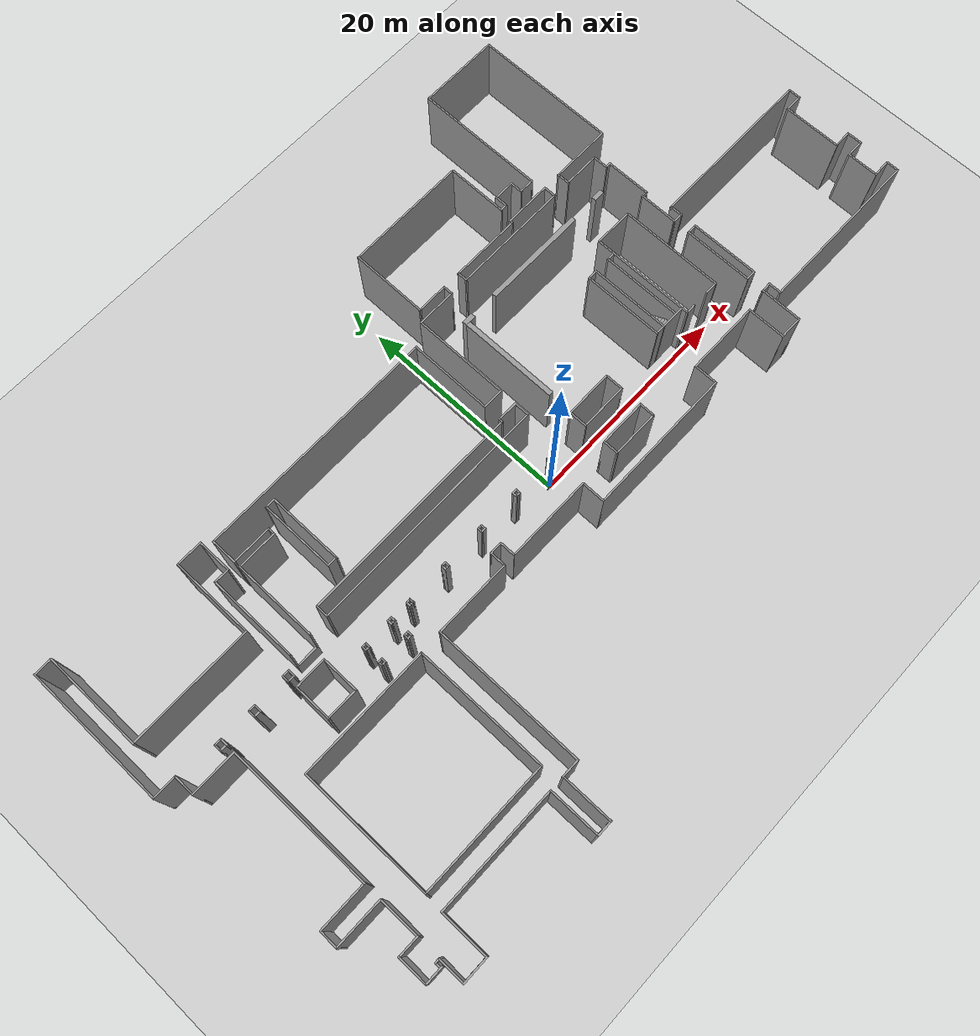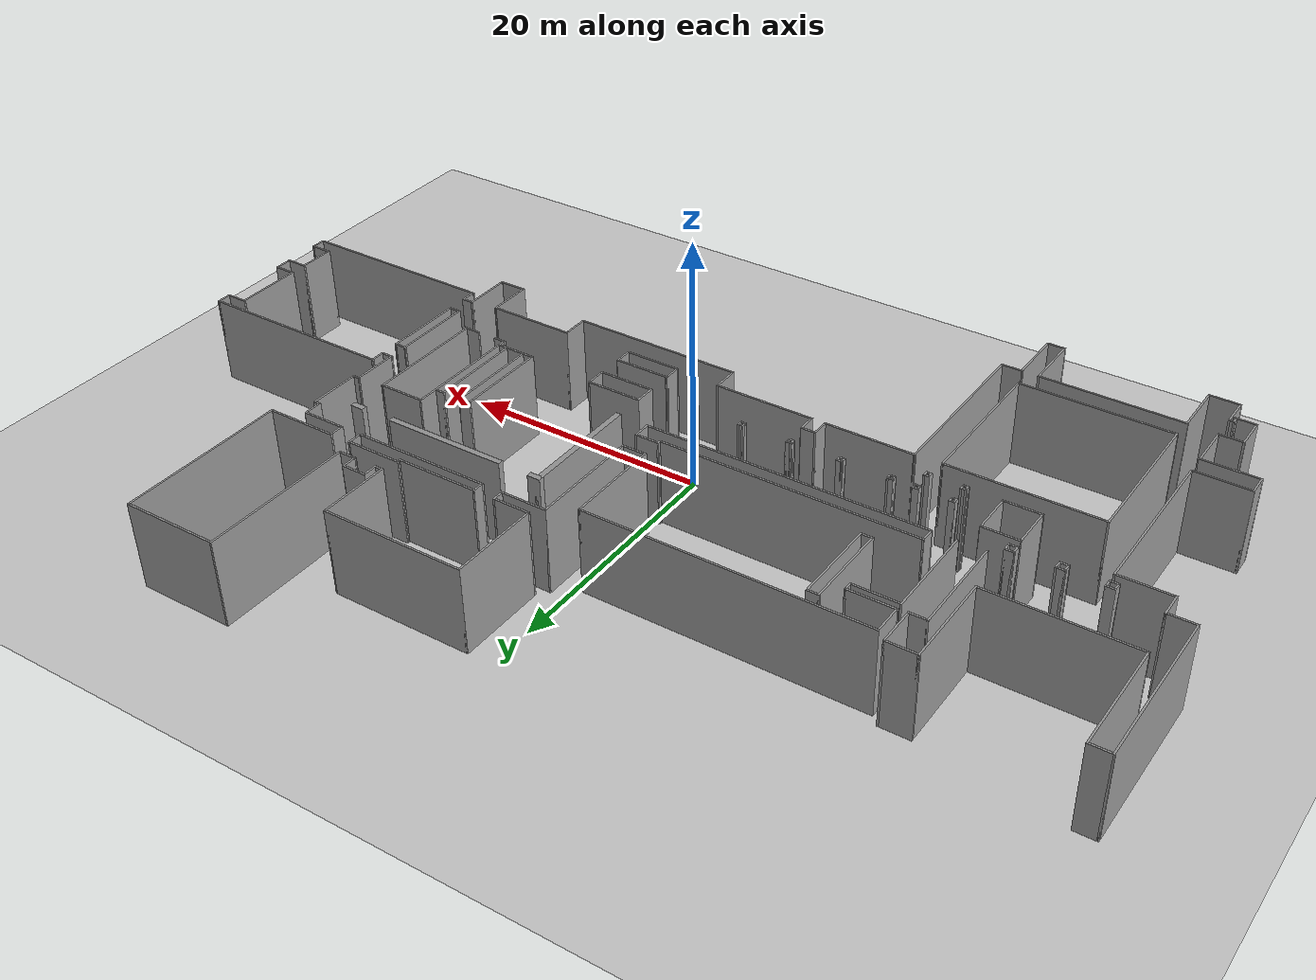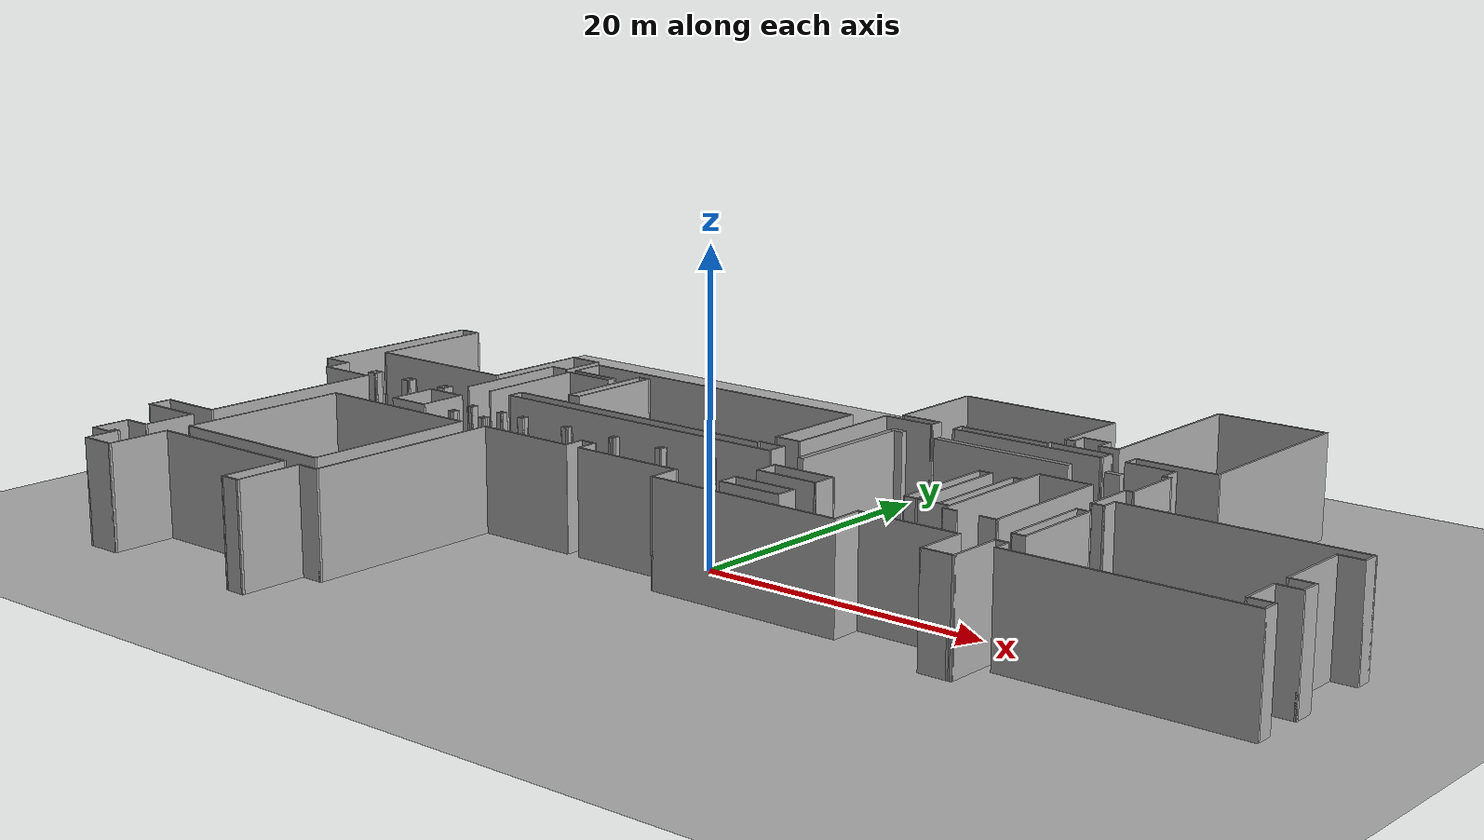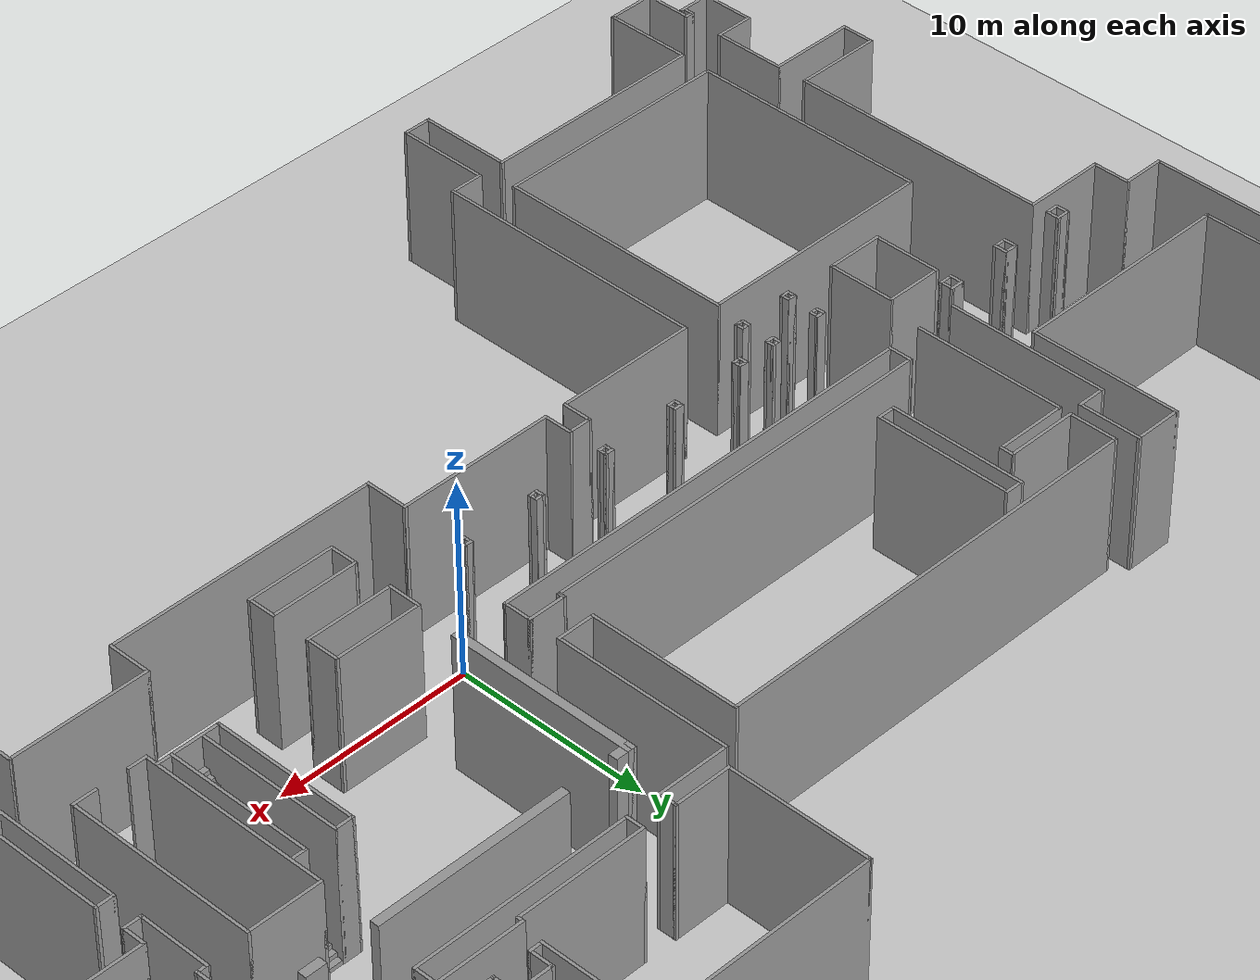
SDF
<sdf version="1.6">
 <world name="default">
  <light name="sun" type="directional">
   <pose>0 0 10 0 -0 0</pose>
   <diffuse>0.8 0.8 0.8 1</diffuse>
   <specular>0.2 0.2 0.2 1</specular>
   <attenuation>
    <range>1000</range>
    <constant>0.9</constant>
    <linear>0.01</linear>
    <quadratic>0.001</quadratic>
   </attenuation>
   <direction>-0.5 0.1 -0.9</direction>
  </light>
  <model name="ground_plane">
   <static>1</static>
   <link name="link">
    <collision name="collision">
     <geometry><plane><normal>0 0 1</normal><size>100 100</size></plane></geometry>
     <surface>
      <contact><collide_bitmask>65535</collide_bitmask></contact>
      <friction><ode><mu>100</mu><mu2>50</mu2></ode></friction>
     </surface>
    </collision>
    <visual name="visual">
     <cast_shadows>0</cast_shadows>
     <geometry><plane><normal>0 0 1</normal><size>100 100</size></plane></geometry>
     <material>
      <script><uri>file://media/materials/scripts/gazebo.material</uri><name>Gazebo/Grey</name></script>
     </material>
    </visual>
   </link>
  </model>
  <gravity>0 0 -9.8</gravity>
  <magnetic_field>6e-06 2.3e-05 -4.2e-05</magnetic_field>
  <atmosphere type="adiabatic"/>
  <physics name="default_physics" default="0" type="ode">
   <max_step_size>0.001</max_step_size>
   <real_time_factor>1</real_time_factor>
   <real_time_update_rate>1000</real_time_update_rate>
  </physics>
  <scene><ambient>0.4 0.4 0.4 1</ambient><background>0.7 0.7 0.7 1</background><shadows>1</shadows></scene>
  <audio><device>default</device></audio>
  <spherical_coordinates>
   <surface_model>EARTH_WGS84</surface_model>
   <latitude_deg>0</latitude_deg>
   <longitude_deg>0</longitude_deg>
   <elevation>0</elevation>
   <heading_deg>0</heading_deg>
  </spherical_coordinates>
  <model name="mmca">
   <pose>0.137385 4.31033 0 0 -0 0</pose>
   <link name="Stairs_1">
    <visual name="Stairs_1_Visual_0">
     <pose>15.1202 4.02391 0.11 0 -0 0</pose>
     <geometry><box><size>1.32 0.292 0.22</size></box></geometry>
     <material>
      <script><uri>file://media/materials/scripts/gazebo.material</uri><name>Gazebo/Grey</name></script>
      <ambient>1 1 1 1</ambient>
     </material>
     <meta><layer>0</layer></meta>
    </visual>
    <collision name="Stairs_1_Collision_0">
     <geometry><box><size>1.32 0.292 0.22</size></box></geometry>
     <pose>15.1202 4.02391 0.11 0 -0 0</pose>
    </collision>
    <visual name="Stairs_1_Visual_1">
     <pose>15.1202 3.73191 0.33 0 -0 0</pose>
     <geometry><box><size>1.32 0.292 0.22</size></box></geometry>
     <material>
      <script><uri>file://media/materials/scripts/gazebo.material</uri><name>Gazebo/Grey</name></script>
      <ambient>1 1 1 1</ambient>
     </material>
     <meta><layer>0</layer></meta>
    </visual>
    <collision name="Stairs_1_Collision_1">
     <geometry><box><size>1.32 0.292 0.22</size></box></geometry>
     <pose>15.1202 3.73191 0.33 0 -0 0</pose>
    </collision>
    <visual name="Stairs_1_Visual_2">
     <pose>15.1202 3.43991 0.55 0 -0 0</pose>
     <geometry><box><size>1.32 0.292 0.22</size></box></geometry>
     <material>
      <script><uri>file://media/materials/scripts/gazebo.material</uri><name>Gazebo/Grey</name></script>
      <ambient>1 1 1 1</ambient>
     </material>
     <meta><layer>0</layer></meta>
    </visual>
    <collision name="Stairs_1_Collision_2">
     <geometry><box><size>1.32 0.292 0.22</size></box></geometry>
     <pose>15.1202 3.43991 0.55 0 -0 0</pose>
    </collision>
    <visual name="Stairs_1_Visual_3">
     <pose>15.1202 3.14791 0.77 0 -0 0</pose>
     <geometry><box><size>1.32 0.292 0.22</size></box></geometry>
     <material>
      <script><uri>file://media/materials/scripts/gazebo.material</uri><name>Gazebo/Grey</name></script>
      <ambient>1 1 1 1</ambient>
     </material>
     <meta><layer>0</layer></meta>
    </visual>
    <collision name="Stairs_1_Collision_3">
     <geometry><box><size>1.32 0.292 0.22</size></box></geometry>
     <pose>15.1202 3.14791 0.77 0 -0 0</pose>
    </collision>
    <visual name="Stairs_1_Visual_4">
     <pose>15.1202 2.85591 0.99 0 -0 0</pose>
     <geometry><box><size>1.32 0.292 0.22</size></box></geometry>
     <material>
      <script><uri>file://media/materials/scripts/gazebo.material</uri><name>Gazebo/Grey</name></script>
      <ambient>1 1 1 1</ambient>
     </material>
     <meta><layer>0</layer></meta>
    </visual>
    <collision name="Stairs_1_Collision_4">
     <geometry><box><size>1.32 0.292 0.22</size></box></geometry>
     <pose>15.1202 2.85591 0.99 0 -0 0</pose>
    </collision>
    <visual name="Stairs_1_Visual_5">
     <pose>15.1202 2.56391 1.21 0 -0 0</pose>
     <geometry><box><size>1.32 0.292 0.22</size></box></geometry>
     <material>
      <script><uri>file://media/materials/scripts/gazebo.material</uri><name>Gazebo/Grey</name></script>
      <ambient>1 1 1 1</ambient>
     </material>
     <meta><layer>0</layer></meta>
    </visual>
    <collision name="Stairs_1_Collision_5">
     <geometry><box><size>1.32 0.292 0.22</size></box></geometry>
     <pose>15.1202 2.56391 1.21 0 -0 0</pose>
    </collision>
    <visual name="Stairs_1_Visual_6">
     <pose>15.1202 2.27191 1.43 0 -0 0</pose>
     <geometry><box><size>1.32 0.292 0.22</size></box></geometry>
     <material>
      <script><uri>file://media/materials/scripts/gazebo.material</uri><name>Gazebo/Grey</name></script>
      <ambient>1 1 1 1</ambient>
     </material>
     <meta><layer>0</layer></meta>
    </visual>
    <collision name="Stairs_1_Collision_6">
     <geometry><box><size>1.32 0.292 0.22</size></box></geometry>
     <pose>15.1202 2.27191 1.43 0 -0 0</pose>
    </collision>
    <visual name="Stairs_1_Visual_7">
     <pose>15.1202 1.97991 1.65 0 -0 0</pose>
     <geometry><box><size>1.32 0.292 0.22</size></box></geometry>
     <material>
      <script><uri>file://media/materials/scripts/gazebo.material</uri><name>Gazebo/Grey</name></script>
      <ambient>1 1 1 1</ambient>
     </material>
     <meta><layer>0</layer></meta>
    </visual>
    <collision name="Stairs_1_Collision_7">
     <geometry><box><size>1.32 0.292 0.22</size></box></geometry>
     <pose>15.1202 1.97991 1.65 0 -0 0</pose>
    </collision>
    <visual name="Stairs_1_Visual_8">
     <pose>15.1202 1.68791 1.87 0 -0 0</pose>
     <geometry><box><size>1.32 0.292 0.22</size></box></geometry>
     <material>
      <script><uri>file://media/materials/scripts/gazebo.material</uri><name>Gazebo/Grey</name></script>
      <ambient>1 1 1 1</ambient>
     </material>
     <meta><layer>0</layer></meta>
    </visual>
    <collision name="Stairs_1_Collision_8">
     <geometry><box><size>1.32 0.292 0.22</size></box></geometry>
     <pose>15.1202 1.68791 1.87 0 -0 0</pose>
    </collision>
    <visual name="Stairs_1_Visual_9">
     <pose>15.1202 1.39591 2.09 0 -0 0</pose>
     <geometry><box><size>1.32 0.292 0.22</size></box></geometry>
     <material>
      <script><uri>file://media/materials/scripts/gazebo.material</uri><name>Gazebo/Grey</name></script>
      <ambient>1 1 1 1</ambient>
     </material>
     <meta><layer>0</layer></meta>
    </visual>
    <collision name="Stairs_1_Collision_9">
     <geometry><box><size>1.32 0.292 0.22</size></box></geometry>
     <pose>15.1202 1.39591 2.09 0 -0 0</pose>
    </collision>
    <visual name="Stairs_1_Visual_10">
     <pose>15.1202 1.10391 2.31 0 -0 0</pose>
     <geometry><box><size>1.32 0.292 0.22</size></box></geometry>
     <material>
      <script><uri>file://media/materials/scripts/gazebo.material</uri><name>Gazebo/Grey</name></script>
      <ambient>1 1 1 1</ambient>
     </material>
     <meta><layer>0</layer></meta>
    </visual>
    <collision name="Stairs_1_Collision_10">
     <geometry><box><size>1.32 0.292 0.22</size></box></geometry>
     <pose>15.1202 1.10391 2.31 0 -0 0</pose>
    </collision>
    <visual name="Stairs_1_Visual_11">
     <pose>15.1202 0.811911 2.53 0 -0 0</pose>
     <geometry><box><size>1.32 0.292 0.22</size></box></geometry>
     <material>
      <script><uri>file://media/materials/scripts/gazebo.material</uri><name>Gazebo/Grey</name></script>
      <ambient>1 1 1 1</ambient>
     </material>
     <meta><layer>0</layer></meta>
    </visual>
    <collision name="Stairs_1_Collision_11">
     <geometry><box><size>1.32 0.292 0.22</size></box></geometry>
     <pose>15.1202 0.811911 2.53 0 -0 0</pose>
    </collision>
    <visual name="Stairs_1_Visual_12">
     <pose>15.1202 0.519911 2.75 0 -0 0</pose>
     <geometry><box><size>1.32 0.292 0.22</size></box></geometry>
     <material>
      <script><uri>file://media/materials/scripts/gazebo.material</uri><name>Gazebo/Grey</name></script>
      <ambient>1 1 1 1</ambient>
     </material>
     <meta><layer>0</layer></meta>
    </visual>
    <collision name="Stairs_1_Collision_12">
     <geometry><box><size>1.32 0.292 0.22</size></box></geometry>
     <pose>15.1202 0.519911 2.75 0 -0 0</pose>
    </collision>
    <visual name="Stairs_1_Visual_13">
     <pose>15.1202 0.227911 2.97 0 -0 0</pose>
     <geometry><box><size>1.32 0.292 0.22</size></box></geometry>
     <material>
      <script><uri>file://media/materials/scripts/gazebo.material</uri><name>Gazebo/Grey</name></script>
      <ambient>1 1 1 1</ambient>
     </material>
     <meta><layer>0</layer></meta>
    </visual>
    <collision name="Stairs_1_Collision_13">
     <geometry><box><size>1.32 0.292 0.22</size></box></geometry>
     <pose>15.1202 0.227911 2.97 0 -0 0</pose>
    </collision>
    <visual name="Stairs_1_Visual_14">
     <pose>15.1202 -0.064089 3.19 0 -0 0</pose>
     <geometry><box><size>1.32 0.292 0.22</size></box></geometry>
     <material>
      <script><uri>file://media/materials/scripts/gazebo.material</uri><name>Gazebo/Grey</name></script>
      <ambient>1 1 1 1</ambient>
     </material>
     <meta><layer>0</layer></meta>
    </visual>
    <collision name="Stairs_1_Collision_14">
     <geometry><box><size>1.32 0.292 0.22</size></box></geometry>
     <pose>15.1202 -0.064089 3.19 0 -0 0</pose>
    </collision>
    <visual name="Stairs_1_Visual_15">
     <pose>15.1202 -0.356089 3.41 0 -0 0</pose>
     <geometry><box><size>1.32 0.292 0.22</size></box></geometry>
     <material>
      <script><uri>file://media/materials/scripts/gazebo.material</uri><name>Gazebo/Grey</name></script>
      <ambient>1 1 1 1</ambient>
     </material>
     <meta><layer>0</layer></meta>
    </visual>
    <collision name="Stairs_1_Collision_15">
     <geometry><box><size>1.32 0.292 0.22</size></box></geometry>
     <pose>15.1202 -0.356089 3.41 0 -0 0</pose>
    </collision>
    <visual name="Stairs_1_Visual_16">
     <pose>15.1202 -0.648088 3.63 0 -0 0</pose>
     <geometry><box><size>1.32 0.292 0.22</size></box></geometry>
     <material>
      <script><uri>file://media/materials/scripts/gazebo.material</uri><name>Gazebo/Grey</name></script>
      <ambient>1 1 1 1</ambient>
     </material>
     <meta><layer>0</layer></meta>
    </visual>
    <collision name="Stairs_1_Collision_16">
     <geometry><box><size>1.32 0.292 0.22</size></box></geometry>
     <pose>15.1202 -0.648088 3.63 0 -0 0</pose>
    </collision>
    <visual name="Stairs_1_Visual_17">
     <pose>15.1202 -0.940089 3.85 0 -0 0</pose>
     <geometry><box><size>1.32 0.292 0.22</size></box></geometry>
     <material>
      <script><uri>file://media/materials/scripts/gazebo.material</uri><name>Gazebo/Grey</name></script>
      <ambient>1 1 1 1</ambient>
     </material>
     <meta><layer>0</layer></meta>
    </visual>
    <collision name="Stairs_1_Collision_17">
     <geometry><box><size>1.32 0.292 0.22</size></box></geometry>
     <pose>15.1202 -0.940089 3.85 0 -0 0</pose>
    </collision>
    <visual name="Stairs_1_Visual_18">
     <pose>15.1202 -1.23209 4.07 0 -0 0</pose>
     <geometry><box><size>1.32 0.292 0.22</size></box></geometry>
     <material>
      <script><uri>file://media/materials/scripts/gazebo.material</uri><name>Gazebo/Grey</name></script>
      <ambient>1 1 1 1</ambient>
     </material>
     <meta><layer>0</layer></meta>
    </visual>
    <collision name="Stairs_1_Collision_18">
     <geometry><box><size>1.32 0.292 0.22</size></box></geometry>
     <pose>15.1202 -1.23209 4.07 0 -0 0</pose>
    </collision>
    <visual name="Stairs_1_Visual_19">
     <pose>15.1202 -1.52409 4.29 0 -0 0</pose>
     <geometry><box><size>1.32 0.292 0.22</size></box></geometry>
     <material>
      <script><uri>file://media/materials/scripts/gazebo.material</uri><name>Gazebo/Grey</name></script>
      <ambient>1 1 1 1</ambient>
     </material>
     <meta><layer>0</layer></meta>
    </visual>
    <collision name="Stairs_1_Collision_19">
     <geometry><box><size>1.32 0.292 0.22</size></box></geometry>
     <pose>15.1202 -1.52409 4.29 0 -0 0</pose>
    </collision>
    <visual name="Stairs_1_Visual_20">
     <pose>15.1202 -1.81609 4.51 0 -0 0</pose>
     <geometry><box><size>1.32 0.292 0.22</size></box></geometry>
     <material>
      <script><uri>file://media/materials/scripts/gazebo.material</uri><name>Gazebo/Grey</name></script>
      <ambient>1 1 1 1</ambient>
     </material>
     <meta><layer>0</layer></meta>
    </visual>
    <collision name="Stairs_1_Collision_20">
     <geometry><box><size>1.32 0.292 0.22</size></box></geometry>
     <pose>15.1202 -1.81609 4.51 0 -0 0</pose>
    </collision>
    <visual name="Stairs_1_Visual_21">
     <pose>15.1202 -2.10809 4.73 0 -0 0</pose>
     <geometry><box><size>1.32 0.292 0.22</size></box></geometry>
     <material>
      <script><uri>file://media/materials/scripts/gazebo.material</uri><name>Gazebo/Grey</name></script>
      <ambient>1 1 1 1</ambient>
     </material>
     <meta><layer>0</layer></meta>
    </visual>
    <collision name="Stairs_1_Collision_21">
     <geometry><box><size>1.32 0.292 0.22</size></box></geometry>
     <pose>15.1202 -2.10809 4.73 0 -0 0</pose>
    </collision>
    <visual name="Stairs_1_Visual_22">
     <pose>15.1202 -2.40009 4.95 0 -0 0</pose>
     <geometry><box><size>1.32 0.292 0.22</size></box></geometry>
     <material>
      <script><uri>file://media/materials/scripts/gazebo.material</uri><name>Gazebo/Grey</name></script>
      <ambient>1 1 1 1</ambient>
     </material>
     <meta><layer>0</layer></meta>
    </visual>
    <collision name="Stairs_1_Collision_22">
     <geometry><box><size>1.32 0.292 0.22</size></box></geometry>
     <pose>15.1202 -2.40009 4.95 0 -0 0</pose>
    </collision>
    <visual name="Stairs_1_Visual_23">
     <pose>15.1202 -2.69209 5.17 0 -0 0</pose>
     <geometry><box><size>1.32 0.292 0.22</size></box></geometry>
     <material>
      <script><uri>file://media/materials/scripts/gazebo.material</uri><name>Gazebo/Grey</name></script>
      <ambient>1 1 1 1</ambient>
     </material>
     <meta><layer>0</layer></meta>
    </visual>
    <collision name="Stairs_1_Collision_23">
     <geometry><box><size>1.32 0.292 0.22</size></box></geometry>
     <pose>15.1202 -2.69209 5.17 0 -0 0</pose>
    </collision>
    <visual name="Stairs_1_Visual_24">
     <pose>15.1202 -2.98409 5.39 0 -0 0</pose>
     <geometry><box><size>1.32 0.292 0.22</size></box></geometry>
     <material>
      <script><uri>file://media/materials/scripts/gazebo.material</uri><name>Gazebo/Grey</name></script>
      <ambient>1 1 1 1</ambient>
     </material>
     <meta><layer>0</layer></meta>
    </visual>
    <collision name="Stairs_1_Collision_24">
     <geometry><box><size>1.32 0.292 0.22</size></box></geometry>
     <pose>15.1202 -2.98409 5.39 0 -0 0</pose>
    </collision>
   </link>
   <link name="Wall_100">
    <collision name="Wall_100_Collision">
     <geometry><box><size>2.5 0.15 7</size></box></geometry>
     <pose>0 0 3.5 0 -0 0</pose>
    </collision>
    <visual name="Wall_100_Visual">
     <pose>0 0 3.5 0 -0 0</pose>
     <geometry><box><size>2.5 0.15 7</size></box></geometry>
     <material>
      <script><uri>file://media/materials/scripts/gazebo.material</uri><name>Gazebo/Grey</name></script>
      <ambient>1 1 1 1</ambient>
     </material>
     <meta><layer>0</layer></meta>
    </visual>
    <pose>-24.9515 10.8265 0 0 -0 3.14159</pose>
   </link>
   <link name="Wall_101">
    <collision name="Wall_101_Collision">
     <geometry><box><size>7.75 0.15 7</size></box></geometry>
     <pose>0 0 3.5 0 -0 0</pose>
    </collision>
    <visual name="Wall_101_Visual">
     <pose>0 0 3.5 0 -0 0</pose>
     <geometry><box><size>7.75 0.15 7</size></box></geometry>
     <material>
      <script><uri>file://media/materials/scripts/gazebo.material</uri><name>Gazebo/Grey</name></script>
      <ambient>1 1 1 1</ambient>
     </material>
     <meta><layer>0</layer></meta>
    </visual>
    <pose>-26.1265 7.0265 0 0 -0 -1.5708</pose>
   </link>
   <link name="Wall_102">
    <collision name="Wall_102_Collision">
     <geometry><box><size>11.5 0.15 7</size></box></geometry>
     <pose>0 0 3.5 0 -0 0</pose>
    </collision>
    <visual name="Wall_102_Visual">
     <pose>0 0 3.5 0 -0 0</pose>
     <geometry><box><size>11.5 0.15 7</size></box></geometry>
     <material>
      <script><uri>file://media/materials/scripts/gazebo.material</uri><name>Gazebo/Grey</name></script>
      <ambient>1 1 1 1</ambient>
     </material>
     <meta><layer>0</layer></meta>
    </visual>
    <pose>-31.8015 3.2265 0 0 -0 3.14159</pose>
   </link>
   <link name="Wall_103">
    <collision name="Wall_103_Collision">
     <geometry><box><size>9.25 0.15 7</size></box></geometry>
     <pose>0 0 3.5 0 -0 0</pose>
    </collision>
    <visual name="Wall_103_Visual">
     <pose>0 0 3.5 0 -0 0</pose>
     <geometry><box><size>9.25 0.15 7</size></box></geometry>
     <material>
      <script><uri>file://media/materials/scripts/gazebo.material</uri><name>Gazebo/Grey</name></script>
      <ambient>1 1 1 1</ambient>
     </material>
     <meta><layer>0</layer></meta>
    </visual>
    <pose>-37.4765 7.7765 0 0 -0 1.5708</pose>
   </link>
   <link name="Wall_104">
    <collision name="Wall_104_Collision">
     <geometry><box><size>1.75 0.15 7</size></box></geometry>
     <pose>0 0 3.5 0 -0 0</pose>
    </collision>
    <visual name="Wall_104_Visual">
     <pose>0 0 3.5 0 -0 0</pose>
     <geometry><box><size>1.75 0.15 7</size></box></geometry>
     <material>
      <script><uri>file://media/materials/scripts/gazebo.material</uri><name>Gazebo/Grey</name></script>
      <ambient>1 1 1 1</ambient>
     </material>
     <meta><layer>0</layer></meta>
    </visual>
    <pose>-38.2765 12.3265 0 0 -0 3.14159</pose>
   </link>
   <link name="Wall_105">
    <collision name="Wall_105_Collision">
     <geometry><box><size>13.25 0.15 7</size></box></geometry>
     <pose>0 0 3.5 0 -0 0</pose>
    </collision>
    <visual name="Wall_105_Visual">
     <pose>0 0 3.5 0 -0 0</pose>
     <geometry><box><size>13.25 0.15 7</size></box></geometry>
     <material>
      <script><uri>file://media/materials/scripts/gazebo.material</uri><name>Gazebo/Grey</name></script>
      <ambient>1 1 1 1</ambient>
     </material>
     <meta><layer>0</layer></meta>
    </visual>
    <pose>-39.0765 5.7765 0 0 -0 -1.5708</pose>
   </link>
   <link name="Wall_106">
    <collision name="Wall_106_Collision">
     <geometry><box><size>2.25 0.15 7</size></box></geometry>
     <pose>0 0 3.5 0 -0 0</pose>
    </collision>
    <visual name="Wall_106_Visual">
     <pose>0 0 3.5 0 -0 0</pose>
     <geometry><box><size>2.25 0.15 7</size></box></geometry>
     <material>
      <script><uri>file://media/materials/scripts/gazebo.material</uri><name>Gazebo/Grey</name></script>
      <ambient>1 1 1 1</ambient>
     </material>
     <meta><layer>0</layer></meta>
    </visual>
    <pose>-38.0265 -0.773501 0 0 -0 0</pose>
   </link>
   <link name="Wall_107">
    <collision name="Wall_107_Collision">
     <geometry><box><size>2 0.15 7</size></box></geometry>
     <pose>0 0 3.5 0 -0 0</pose>
    </collision>
    <visual name="Wall_107_Visual">
     <pose>0 0 3.5 0 -0 0</pose>
     <geometry><box><size>2 0.15 7</size></box></geometry>
     <material>
      <script><uri>file://media/materials/scripts/gazebo.material</uri><name>Gazebo/Grey</name></script>
      <ambient>1 1 1 1</ambient>
     </material>
     <meta><layer>0</layer></meta>
    </visual>
    <pose>-36.9765 -1.6985 0 0 -0 -1.5708</pose>
   </link>
   <link name="Wall_108">
    <collision name="Wall_108_Collision">
     <geometry><box><size>4.25 0.15 7</size></box></geometry>
     <pose>0 0 3.5 0 -0 0</pose>
    </collision>
    <visual name="Wall_108_Visual">
     <pose>0 0 3.5 0 -0 0</pose>
     <geometry><box><size>4.25 0.15 7</size></box></geometry>
     <material>
      <script><uri>file://media/materials/scripts/gazebo.material</uri><name>Gazebo/Grey</name></script>
      <ambient>1 1 1 1</ambient>
     </material>
     <meta><layer>0</layer></meta>
    </visual>
    <pose>-34.9265 -2.6235 0 0 -0 0</pose>
   </link>
   <link name="Wall_109">
    <collision name="Wall_109_Collision">
     <geometry><box><size>13.5 0.15 7</size></box></geometry>
     <pose>0 0 3.5 0 -0 0</pose>
    </collision>
    <visual name="Wall_109_Visual">
     <pose>0 0 3.5 0 -0 0</pose>
     <geometry><box><size>13.5 0.15 7</size></box></geometry>
     <material>
      <script><uri>file://media/materials/scripts/gazebo.material</uri><name>Gazebo/Grey</name></script>
      <ambient>1 1 1 1</ambient>
     </material>
     <meta><layer>0</layer></meta>
    </visual>
    <pose>-32.8765 -9.2985 0 0 -0 -1.5708</pose>
   </link>
   <link name="Wall_110">
    <collision name="Wall_110_Collision">
     <geometry><box><size>4.5 0.15 7</size></box></geometry>
     <pose>0 0 3.5 0 -0 0</pose>
    </collision>
    <visual name="Wall_110_Visual">
     <pose>0 0 3.5 0 -0 0</pose>
     <geometry><box><size>4.5 0.15 7</size></box></geometry>
     <material>
      <script><uri>file://media/materials/scripts/gazebo.material</uri><name>Gazebo/Grey</name></script>
      <ambient>1 1 1 1</ambient>
     </material>
     <meta><layer>0</layer></meta>
    </visual>
    <pose>-35.0515 -15.9735 0 0 -0 3.14159</pose>
   </link>
   <link name="Wall_111">
    <collision name="Wall_111_Collision">
     <geometry><box><size>1.75 0.15 7</size></box></geometry>
     <pose>0 0 3.5 0 -0 0</pose>
    </collision>
    <visual name="Wall_111_Visual">
     <pose>0 0 3.5 0 -0 0</pose>
     <geometry><box><size>1.75 0.15 7</size></box></geometry>
     <material>
      <script><uri>file://media/materials/scripts/gazebo.material</uri><name>Gazebo/Grey</name></script>
      <ambient>1 1 1 1</ambient>
     </material>
     <meta><layer>0</layer></meta>
    </visual>
    <pose>-37.2265 -16.7735 0 0 -0 -1.5708</pose>
   </link>
   <link name="Wall_112">
    <collision name="Wall_112_Collision">
     <geometry><box><size>4.5 0.15 7</size></box></geometry>
     <pose>0 0 3.5 0 -0 0</pose>
    </collision>
    <visual name="Wall_112_Visual">
     <pose>0 0 3.5 0 -0 0</pose>
     <geometry><box><size>4.5 0.15 7</size></box></geometry>
     <material>
      <script><uri>file://media/materials/scripts/gazebo.material</uri><name>Gazebo/Grey</name></script>
      <ambient>1 1 1 1</ambient>
     </material>
     <meta><layer>0</layer></meta>
    </visual>
    <pose>-35.0515 -17.5735 0 0 -0 0</pose>
   </link>
   <link name="Wall_113">
    <collision name="Wall_113_Collision">
     <geometry><box><size>3.75 0.15 7</size></box></geometry>
     <pose>0 0 3.5 0 -0 0</pose>
    </collision>
    <visual name="Wall_113_Visual">
     <pose>0 0 3.5 0 -0 0</pose>
     <geometry><box><size>3.75 0.15 7</size></box></geometry>
     <material>
      <script><uri>file://media/materials/scripts/gazebo.material</uri><name>Gazebo/Grey</name></script>
      <ambient>1 1 1 1</ambient>
     </material>
     <meta><layer>0</layer></meta>
    </visual>
    <pose>-32.8765 -19.3735 0 0 -0 -1.5708</pose>
   </link>
   <link name="Wall_114">
    <collision name="Wall_114_Collision">
     <geometry><box><size>2 0.15 7</size></box></geometry>
     <pose>0 0 3.5 0 -0 0</pose>
    </collision>
    <visual name="Wall_114_Visual">
     <pose>0 0 3.5 0 -0 0</pose>
     <geometry><box><size>2 0.15 7</size></box></geometry>
     <material>
      <script><uri>file://media/materials/scripts/gazebo.material</uri><name>Gazebo/Grey</name></script>
      <ambient>1 1 1 1</ambient>
     </material>
     <meta><layer>0</layer></meta>
    </visual>
    <pose>-33.8015 -21.1735 0 0 -0 3.14159</pose>
   </link>
   <link name="Wall_116">
    <collision name="Wall_116_Collision">
     <geometry><box><size>2.75 0.15 7</size></box></geometry>
     <pose>0 0 3.5 0 -0 0</pose>
    </collision>
    <visual name="Wall_116_Visual">
     <pose>0 0 3.5 0 -0 0</pose>
     <geometry><box><size>2.75 0.15 7</size></box></geometry>
     <material>
      <script><uri>file://media/materials/scripts/gazebo.material</uri><name>Gazebo/Grey</name></script>
      <ambient>1 1 1 1</ambient>
     </material>
     <meta><layer>0</layer></meta>
    </visual>
    <pose>-34.7265 -22.4735 0 0 -0 -1.5708</pose>
   </link>
   <link name="Wall_117">
    <collision name="Wall_117_Collision">
     <geometry><box><size>1.75 0.15 7</size></box></geometry>
     <pose>0 0 3.5 0 -0 0</pose>
    </collision>
    <visual name="Wall_117_Visual">
     <pose>0 0 3.5 0 -0 0</pose>
     <geometry><box><size>1.75 0.15 7</size></box></geometry>
     <material>
      <script><uri>file://media/materials/scripts/gazebo.material</uri><name>Gazebo/Grey</name></script>
      <ambient>1 1 1 1</ambient>
     </material>
     <meta><layer>0</layer></meta>
    </visual>
    <pose>-33.9265 -23.7735 0 0 -0 0</pose>
   </link>
   <link name="Wall_119">
    <collision name="Wall_119_Collision">
     <geometry><box><size>1.75 0.15 7</size></box></geometry>
     <pose>0 0 3.5 0 -0 0</pose>
    </collision>
    <visual name="Wall_119_Visual">
     <pose>0 0 3.5 0 -0 0</pose>
     <geometry><box><size>1.75 0.15 7</size></box></geometry>
     <material>
      <script><uri>file://media/materials/scripts/gazebo.material</uri><name>Gazebo/Grey</name></script>
      <ambient>1 1 1 1</ambient>
     </material>
     <meta><layer>0</layer></meta>
    </visual>
    <pose>3.5775 -3.5445 0 0 -0 -1.5708</pose>
   </link>
   <link name="Wall_120">
    <collision name="Wall_120_Collision">
     <geometry><box><size>4.5 0.15 7</size></box></geometry>
     <pose>0 0 3.5 0 -0 0</pose>
    </collision>
    <visual name="Wall_120_Visual">
     <pose>0 0 3.5 0 -0 0</pose>
     <geometry><box><size>4.5 0.15 7</size></box></geometry>
     <material>
      <script><uri>file://media/materials/scripts/gazebo.material</uri><name>Gazebo/Grey</name></script>
      <ambient>1 1 1 1</ambient>
     </material>
     <meta><layer>0</layer></meta>
    </visual>
    <pose>5.7525 -4.3445 0 0 -0 0</pose>
   </link>
   <link name="Wall_121">
    <collision name="Wall_121_Collision">
     <geometry><box><size>1.75 0.15 7</size></box></geometry>
     <pose>0 0 3.5 0 -0 0</pose>
    </collision>
    <visual name="Wall_121_Visual">
     <pose>0 0 3.5 0 -0 0</pose>
     <geometry><box><size>1.75 0.15 7</size></box></geometry>
     <material>
      <script><uri>file://media/materials/scripts/gazebo.material</uri><name>Gazebo/Grey</name></script>
      <ambient>1 1 1 1</ambient>
     </material>
     <meta><layer>0</layer></meta>
    </visual>
    <pose>7.9275 -3.5445 0 0 -0 1.5708</pose>
   </link>
   <link name="Wall_122">
    <collision name="Wall_122_Collision">
     <geometry><box><size>4.5 0.15 7</size></box></geometry>
     <pose>0 0 3.5 0 -0 0</pose>
    </collision>
    <visual name="Wall_122_Visual">
     <pose>0 0 3.5 0 -0 0</pose>
     <geometry><box><size>4.5 0.15 7</size></box></geometry>
     <material>
      <script><uri>file://media/materials/scripts/gazebo.material</uri><name>Gazebo/Grey</name></script>
      <ambient>1 1 1 1</ambient>
     </material>
     <meta><layer>0</layer></meta>
    </visual>
    <pose>5.7525 -2.7445 0 0 -0 3.14159</pose>
   </link>
   <link name="Wall_124">
    <collision name="Wall_124_Collision">
     <geometry><box><size>4.5 0.15 7</size></box></geometry>
     <pose>0 0 3.5 0 -0 0</pose>
    </collision>
    <visual name="Wall_124_Visual">
     <pose>0 0 3.5 0 -0 0</pose>
     <geometry><box><size>4.5 0.15 7</size></box></geometry>
     <material>
      <script><uri>file://media/materials/scripts/gazebo.material</uri><name>Gazebo/Grey</name></script>
      <ambient>1 1 1 1</ambient>
     </material>
     <meta><layer>0</layer></meta>
    </visual>
    <pose>5.7375 -6.3445 0 0 -0 0</pose>
   </link>
   <link name="Wall_125">
    <collision name="Wall_125_Collision">
     <geometry><box><size>1.5 0.15 7</size></box></geometry>
     <pose>0 0 3.5 0 -0 0</pose>
    </collision>
    <visual name="Wall_125_Visual">
     <pose>0 0 3.5 0 -0 0</pose>
     <geometry><box><size>1.5 0.15 7</size></box></geometry>
     <material>
      <script><uri>file://media/materials/scripts/gazebo.material</uri><name>Gazebo/Grey</name></script>
      <ambient>1 1 1 1</ambient>
     </material>
     <meta><layer>0</layer></meta>
    </visual>
    <pose>7.9125 -7.0195 0 0 -0 -1.5708</pose>
   </link>
   <link name="Wall_126">
    <collision name="Wall_126_Collision">
     <geometry><box><size>4.5 0.15 7</size></box></geometry>
     <pose>0 0 3.5 0 -0 0</pose>
    </collision>
    <visual name="Wall_126_Visual">
     <pose>0 0 3.5 0 -0 0</pose>
     <geometry><box><size>4.5 0.15 7</size></box></geometry>
     <material>
      <script><uri>file://media/materials/scripts/gazebo.material</uri><name>Gazebo/Grey</name></script>
      <ambient>1 1 1 1</ambient>
     </material>
     <meta><layer>0</layer></meta>
    </visual>
    <pose>5.7375 -7.6945 0 0 -0 3.14159</pose>
   </link>
   <link name="Wall_127">
    <collision name="Wall_127_Collision">
     <geometry><box><size>1.5 0.15 7</size></box></geometry>
     <pose>0 0 3.5 0 -0 0</pose>
    </collision>
    <visual name="Wall_127_Visual">
     <pose>0 0 3.5 0 -0 0</pose>
     <geometry><box><size>1.5 0.15 7</size></box></geometry>
     <material>
      <script><uri>file://media/materials/scripts/gazebo.material</uri><name>Gazebo/Grey</name></script>
      <ambient>1 1 1 1</ambient>
     </material>
     <meta><layer>0</layer></meta>
    </visual>
    <pose>3.5625 -7.0195 0 0 -0 1.5708</pose>
   </link>
   <link name="Wall_129">
    <collision name="Wall_129_Collision">
     <geometry><box><size>9.55 0.45 7</size></box></geometry>
     <pose>0 0 3.5 0 -0 0</pose>
    </collision>
    <visual name="Wall_129_Visual">
     <pose>0 0 3.5 0 -0 0</pose>
     <geometry><box><size>9.55 0.45 7</size></box></geometry>
     <material>
      <script><uri>file://media/materials/scripts/gazebo.material</uri><name>Gazebo/Grey</name></script>
      <ambient>1 1 1 1</ambient>
     </material>
     <meta><layer>0</layer></meta>
    </visual>
    <pose>3.7355 4.2315 0 0 -0 1.5708</pose>
   </link>
   <link name="Wall_131">
    <collision name="Wall_131_Collision">
     <geometry><box><size>1.05014 0.45 7</size></box></geometry>
     <pose>0 0 3.5 0 -0 0</pose>
    </collision>
    <visual name="Wall_131_Visual">
     <pose>0 0 3.5 0 -0 0</pose>
     <geometry><box><size>1.05014 0.45 7</size></box></geometry>
     <material>
      <script><uri>file://media/materials/scripts/gazebo.material</uri><name>Gazebo/Grey</name></script>
      <ambient>1 1 1 1</ambient>
     </material>
     <meta><layer>0</layer></meta>
    </visual>
    <pose>4.0355 8.7815 0 0 -0 0</pose>
   </link>
   <link name="Wall_133">
    <collision name="Wall_133_Collision">
     <geometry><box><size>9.80032 0.45 7</size></box></geometry>
     <pose>0 0 3.5 0 -0 0</pose>
    </collision>
    <visual name="Wall_133_Visual">
     <pose>0 0 3.5 0 -0 0</pose>
     <geometry><box><size>9.80032 0.45 7</size></box></geometry>
     <material>
      <script><uri>file://media/materials/scripts/gazebo.material</uri><name>Gazebo/Grey</name></script>
      <ambient>1 1 1 1</ambient>
     </material>
     <meta><layer>0</layer></meta>
    </visual>
    <pose>11.9185 8.7625 0 0 -0 0</pose>
   </link>
   <link name="Wall_135">
    <collision name="Wall_135_Collision">
     <geometry><box><size>1.05 0.45 7</size></box></geometry>
     <pose>0 0 3.5 0 -0 0</pose>
    </collision>
    <visual name="Wall_135_Visual">
     <pose>0 0 3.5 0 -0 0</pose>
     <geometry><box><size>1.05 0.45 7</size></box></geometry>
     <material>
      <script><uri>file://media/materials/scripts/gazebo.material</uri><name>Gazebo/Grey</name></script>
      <ambient>1 1 1 1</ambient>
     </material>
     <meta><layer>0</layer></meta>
    </visual>
    <pose>19.8635 8.7725 0 0 -0 0</pose>
   </link>
   <link name="Wall_148">
    <collision name="Wall_148_Collision">
     <geometry><box><size>1 0.15 7</size></box></geometry>
     <pose>0 0 3.5 0 -0 0</pose>
    </collision>
    <visual name="Wall_148_Visual">
     <pose>0 0 3.5 0 -0 0</pose>
     <geometry><box><size>1 0.15 7</size></box></geometry>
     <material>
      <script><uri>file://media/materials/scripts/gazebo.material</uri><name>Gazebo/Grey</name></script>
      <ambient>1 1 1 1</ambient>
     </material>
     <meta><layer>0</layer></meta>
    </visual>
    <pose>22.8155 -7.0925 0 0 -0 0</pose>
   </link>
   <link name="Wall_149">
    <collision name="Wall_149_Collision">
     <geometry><box><size>1.25 0.15 7</size></box></geometry>
     <pose>0 0 3.5 0 -0 0</pose>
    </collision>
    <visual name="Wall_149_Visual">
     <pose>0 0 3.5 0 -0 0</pose>
     <geometry><box><size>1.25 0.15 7</size></box></geometry>
     <material>
      <script><uri>file://media/materials/scripts/gazebo.material</uri><name>Gazebo/Grey</name></script>
      <ambient>1 1 1 1</ambient>
     </material>
     <meta><layer>0</layer></meta>
    </visual>
    <pose>23.2405 -7.6425 0 0 -0 -1.5708</pose>
   </link>
   <link name="Wall_152">
    <collision name="Wall_152_Collision">
     <geometry><box><size>1 0.15 7</size></box></geometry>
     <pose>0 0 3.5 0 -0 0</pose>
    </collision>
    <visual name="Wall_152_Visual">
     <pose>0 0 3.5 0 -0 0</pose>
     <geometry><box><size>1 0.15 7</size></box></geometry>
     <material>
      <script><uri>file://media/materials/scripts/gazebo.material</uri><name>Gazebo/Grey</name></script>
      <ambient>1 1 1 1</ambient>
     </material>
     <meta><layer>0</layer></meta>
    </visual>
    <pose>22.8035 -5.4755 0 0 -0 0</pose>
   </link>
   <link name="Wall_154">
    <collision name="Wall_154_Collision">
     <geometry><box><size>6.5 0.15 7</size></box></geometry>
     <pose>0 0 3.5 0 -0 0</pose>
    </collision>
    <visual name="Wall_154_Visual">
     <pose>0 0 3.5 0 -0 0</pose>
     <geometry><box><size>6.5 0.15 7</size></box></geometry>
     <material>
      <script><uri>file://media/materials/scripts/gazebo.material</uri><name>Gazebo/Grey</name></script>
      <ambient>1 1 1 1</ambient>
     </material>
     <meta><layer>0</layer></meta>
    </visual>
    <pose>23.2285 -2.3005 0 0 -0 1.5708</pose>
   </link>
   <link name="Wall_155">
    <collision name="Wall_155_Collision">
     <geometry><box><size>1 0.15 7</size></box></geometry>
     <pose>0 0 3.5 0 -0 0</pose>
    </collision>
    <visual name="Wall_155_Visual">
     <pose>0 0 3.5 0 -0 0</pose>
     <geometry><box><size>1 0.15 7</size></box></geometry>
     <material>
      <script><uri>file://media/materials/scripts/gazebo.material</uri><name>Gazebo/Grey</name></script>
      <ambient>1 1 1 1</ambient>
     </material>
     <meta><layer>0</layer></meta>
    </visual>
    <pose>22.8035 0.874499 0 0 -0 3.14159</pose>
   </link>
   <link name="Wall_157">
    <collision name="Wall_157_Collision">
     <geometry><box><size>1 0.15 7</size></box></geometry>
     <pose>0 0 3.5 0 -0 0</pose>
    </collision>
    <visual name="Wall_157_Visual">
     <pose>0 0 3.5 0 -0 0</pose>
     <geometry><box><size>1 0.15 7</size></box></geometry>
     <material>
      <script><uri>file://media/materials/scripts/gazebo.material</uri><name>Gazebo/Grey</name></script>
      <ambient>1 1 1 1</ambient>
     </material>
     <meta><layer>0</layer></meta>
    </visual>
    <pose>22.8015 2.4075 0 0 -0 0</pose>
   </link>
   <link name="Wall_161">
    <collision name="Wall_161_Collision">
     <geometry><box><size>1.75 0.15 7</size></box></geometry>
     <pose>0 0 3.5 0 -0 0</pose>
    </collision>
    <visual name="Wall_161_Visual">
     <pose>0 0 3.5 0 -0 0</pose>
     <geometry><box><size>1.75 0.15 7</size></box></geometry>
     <material>
      <script><uri>file://media/materials/scripts/gazebo.material</uri><name>Gazebo/Grey</name></script>
      <ambient>1 1 1 1</ambient>
     </material>
     <meta><layer>0</layer></meta>
    </visual>
    <pose>38.2765 2.4075 0 0 -0 3.14159</pose>
   </link>
   <link name="Wall_162">
    <collision name="Wall_162_Collision">
     <geometry><box><size>5.5 0.15 7</size></box></geometry>
     <pose>0 0 3.5 0 -0 0</pose>
    </collision>
    <visual name="Wall_162_Visual">
     <pose>0 0 3.5 0 -0 0</pose>
     <geometry><box><size>5.5 0.15 7</size></box></geometry>
     <material>
      <script><uri>file://media/materials/scripts/gazebo.material</uri><name>Gazebo/Grey</name></script>
      <ambient>1 1 1 1</ambient>
     </material>
     <meta><layer>0</layer></meta>
    </visual>
    <pose>37.4765 -0.267501 0 0 -0 -1.5708</pose>
   </link>
   <link name="Wall_163">
    <collision name="Wall_163_Collision">
     <geometry><box><size>1.75 0.15 7</size></box></geometry>
     <pose>0 0 3.5 0 -0 0</pose>
    </collision>
    <visual name="Wall_163_Visual">
     <pose>0 0 3.5 0 -0 0</pose>
     <geometry><box><size>1.75 0.15 7</size></box></geometry>
     <material>
      <script><uri>file://media/materials/scripts/gazebo.material</uri><name>Gazebo/Grey</name></script>
      <ambient>1 1 1 1</ambient>
     </material>
     <meta><layer>0</layer></meta>
    </visual>
    <pose>38.2765 -2.9425 0 0 -0 0</pose>
   </link>
   <link name="Wall_164">
    <collision name="Wall_164_Collision">
     <geometry><box><size>1.5 0.15 7</size></box></geometry>
     <pose>0 0 3.5 0 -0 0</pose>
    </collision>
    <visual name="Wall_164_Visual">
     <pose>0 0 3.5 0 -0 0</pose>
     <geometry><box><size>1.5 0.15 7</size></box></geometry>
     <material>
      <script><uri>file://media/materials/scripts/gazebo.material</uri><name>Gazebo/Grey</name></script>
      <ambient>1 1 1 1</ambient>
     </material>
     <meta><layer>0</layer></meta>
    </visual>
    <pose>39.0765 -3.6175 0 0 -0 -1.5708</pose>
   </link>
   <link name="Wall_165">
    <collision name="Wall_165_Collision">
     <geometry><box><size>1.75 0.15 7</size></box></geometry>
     <pose>0 0 3.5 0 -0 0</pose>
    </collision>
    <visual name="Wall_165_Visual">
     <pose>0 0 3.5 0 -0 0</pose>
     <geometry><box><size>1.75 0.15 7</size></box></geometry>
     <material>
      <script><uri>file://media/materials/scripts/gazebo.material</uri><name>Gazebo/Grey</name></script>
      <ambient>1 1 1 1</ambient>
     </material>
     <meta><layer>0</layer></meta>
    </visual>
    <pose>38.2765 -4.2925 0 0 -0 3.14159</pose>
   </link>
   <link name="Wall_166">
    <collision name="Wall_166_Collision">
     <geometry><box><size>3 0.15 7</size></box></geometry>
     <pose>0 0 3.5 0 -0 0</pose>
    </collision>
    <visual name="Wall_166_Visual">
     <pose>0 0 3.5 0 -0 0</pose>
     <geometry><box><size>3 0.15 7</size></box></geometry>
     <material>
      <script><uri>file://media/materials/scripts/gazebo.material</uri><name>Gazebo/Grey</name></script>
      <ambient>1 1 1 1</ambient>
     </material>
     <meta><layer>0</layer></meta>
    </visual>
    <pose>37.4765 -5.7175 0 0 -0 -1.5708</pose>
   </link>
   <link name="Wall_167">
    <collision name="Wall_167_Collision">
     <geometry><box><size>1.75 0.15 7</size></box></geometry>
     <pose>0 0 3.5 0 -0 0</pose>
    </collision>
    <visual name="Wall_167_Visual">
     <pose>0 0 3.5 0 -0 0</pose>
     <geometry><box><size>1.75 0.15 7</size></box></geometry>
     <material>
      <script><uri>file://media/materials/scripts/gazebo.material</uri><name>Gazebo/Grey</name></script>
      <ambient>1 1 1 1</ambient>
     </material>
     <meta><layer>0</layer></meta>
    </visual>
    <pose>38.2765 -7.1425 0 0 -0 0</pose>
   </link>
   <link name="Wall_168">
    <collision name="Wall_168_Collision">
     <geometry><box><size>1.25 0.15 7</size></box></geometry>
     <pose>0 0 3.5 0 -0 0</pose>
    </collision>
    <visual name="Wall_168_Visual">
     <pose>0 0 3.5 0 -0 0</pose>
     <geometry><box><size>1.25 0.15 7</size></box></geometry>
     <material>
      <script><uri>file://media/materials/scripts/gazebo.material</uri><name>Gazebo/Grey</name></script>
      <ambient>1 1 1 1</ambient>
     </material>
     <meta><layer>0</layer></meta>
    </visual>
    <pose>39.0765 -7.6925 0 0 -0 -1.5708</pose>
   </link>
   <link name="Wall_169">
    <collision name="Wall_169_Collision">
     <geometry><box><size>16 0.15 7</size></box></geometry>
     <pose>0 0 3.5 0 -0 0</pose>
    </collision>
    <visual name="Wall_169_Visual">
     <pose>0 0 3.5 0 -0 0</pose>
     <geometry><box><size>16 0.15 7</size></box></geometry>
     <material>
      <script><uri>file://media/materials/scripts/gazebo.material</uri><name>Gazebo/Grey</name></script>
      <ambient>1 1 1 1</ambient>
     </material>
     <meta><layer>0</layer></meta>
    </visual>
    <pose>31.1515 -8.2425 0 0 -0 3.14159</pose>
   </link>
   <link name="Wall_172">
    <collision name="Wall_172_Collision">
     <geometry><box><size>6.5 0.15 7</size></box></geometry>
     <pose>0 0 3.5 0 -0 0</pose>
    </collision>
    <visual name="Wall_172_Visual">
     <pose>0 0 3.5 0 -0 0</pose>
     <geometry><box><size>6.5 0.15 7</size></box></geometry>
     <material>
      <script><uri>file://media/materials/scripts/gazebo.material</uri><name>Gazebo/Grey</name></script>
      <ambient>1 1 1 1</ambient>
     </material>
     <meta><layer>0</layer></meta>
    </visual>
    <pose>22.3785 -2.3005 0 0 -0 -1.5708</pose>
   </link>
   <link name="Wall_174">
    <collision name="Wall_174_Collision">
     <geometry><box><size>3.93426 0.15 7</size></box></geometry>
     <pose>0 0 3.5 0 -0 0</pose>
    </collision>
    <visual name="Wall_174_Visual">
     <pose>0 0 3.5 0 -0 0</pose>
     <geometry><box><size>3.93426 0.15 7</size></box></geometry>
     <material>
      <script><uri>file://media/materials/scripts/gazebo.material</uri><name>Gazebo/Grey</name></script>
      <ambient>1 1 1 1</ambient>
     </material>
     <meta><layer>0</layer></meta>
    </visual>
    <pose>22.391 -8.9845 0 0 -0 -1.57053</pose>
   </link>
   <link name="Wall_176">
    <collision name="Wall_176_Collision">
     <geometry><box><size>3.71588 0.15 7</size></box></geometry>
     <pose>0 0 3.5 0 -0 0</pose>
    </collision>
    <visual name="Wall_176_Visual">
     <pose>0 0 3.5 0 -0 0</pose>
     <geometry><box><size>3.71588 0.15 7</size></box></geometry>
     <material>
      <script><uri>file://media/materials/scripts/gazebo.material</uri><name>Gazebo/Grey</name></script>
      <ambient>1 1 1 1</ambient>
     </material>
     <meta><layer>0</layer></meta>
    </visual>
    <pose>22.384 4.1905 0 0 -0 -1.575</pose>
   </link>
   <link name="Wall_178">
    <collision name="Wall_178_Collision">
     <geometry><box><size>1.25 0.15 7</size></box></geometry>
     <pose>0 0 3.5 0 -0 0</pose>
    </collision>
    <visual name="Wall_178_Visual">
     <pose>0 0 3.5 0 -0 0</pose>
     <geometry><box><size>1.25 0.15 7</size></box></geometry>
     <material>
      <script><uri>file://media/materials/scripts/gazebo.material</uri><name>Gazebo/Grey</name></script>
      <ambient>1 1 1 1</ambient>
     </material>
     <meta><layer>0</layer></meta>
    </visual>
    <pose>23.2265 2.9575 0 0 -0 1.5708</pose>
   </link>
   <link name="Wall_179">
    <collision name="Wall_179_Collision">
     <geometry><box><size>16 0.15 7</size></box></geometry>
     <pose>0 0 3.5 0 -0 0</pose>
    </collision>
    <visual name="Wall_179_Visual">
     <pose>0 0 3.5 0 -0 0</pose>
     <geometry><box><size>16 0.15 7</size></box></geometry>
     <material>
      <script><uri>file://media/materials/scripts/gazebo.material</uri><name>Gazebo/Grey</name></script>
      <ambient>1 1 1 1</ambient>
     </material>
     <meta><layer>0</layer></meta>
    </visual>
    <pose>31.1515 3.5075 0 0 -0 0</pose>
   </link>
   <link name="Wall_180">
    <collision name="Wall_180_Collision">
     <geometry><box><size>1.25 0.15 7</size></box></geometry>
     <pose>0 0 3.5 0 -0 0</pose>
    </collision>
    <visual name="Wall_180_Visual">
     <pose>0 0 3.5 0 -0 0</pose>
     <geometry><box><size>1.25 0.15 7</size></box></geometry>
     <material>
      <script><uri>file://media/materials/scripts/gazebo.material</uri><name>Gazebo/Grey</name></script>
      <ambient>1 1 1 1</ambient>
     </material>
     <meta><layer>0</layer></meta>
    </visual>
    <pose>39.0765 2.9575 0 0 -0 -1.5708</pose>
   </link>
   <link name="Wall_182">
    <collision name="Wall_182_Collision">
     <geometry><box><size>9 0.15 7</size></box></geometry>
     <pose>0 0 3.5 0 -0 0</pose>
    </collision>
    <visual name="Wall_182_Visual">
     <pose>0 0 3.5 0 -0 0</pose>
     <geometry><box><size>9 0.15 7</size></box></geometry>
     <material>
      <script><uri>file://media/materials/scripts/gazebo.material</uri><name>Gazebo/Grey</name></script>
      <ambient>1 1 1 1</ambient>
     </material>
     <meta><layer>0</layer></meta>
    </visual>
    <pose>1.1735 7.0015 0 0 -0 1.5708</pose>
   </link>
   <link name="Wall_183">
    <collision name="Wall_183_Collision">
     <geometry><box><size>3.75 0.15 7</size></box></geometry>
     <pose>0 0 3.5 0 -0 0</pose>
    </collision>
    <visual name="Wall_183_Visual">
     <pose>0 0 3.5 0 -0 0</pose>
     <geometry><box><size>3.75 0.15 7</size></box></geometry>
     <material>
      <script><uri>file://media/materials/scripts/gazebo.material</uri><name>Gazebo/Grey</name></script>
      <ambient>1 1 1 1</ambient>
     </material>
     <meta><layer>0</layer></meta>
    </visual>
    <pose>2.9735 11.4265 0 0 -0 0</pose>
   </link>
   <link name="Wall_184">
    <collision name="Wall_184_Collision">
     <geometry><box><size>1 0.15 7</size></box></geometry>
     <pose>0 0 3.5 0 -0 0</pose>
    </collision>
    <visual name="Wall_184_Visual">
     <pose>0 0 3.5 0 -0 0</pose>
     <geometry><box><size>1 0.15 7</size></box></geometry>
     <material>
      <script><uri>file://media/materials/scripts/gazebo.material</uri><name>Gazebo/Grey</name></script>
      <ambient>1 1 1 1</ambient>
     </material>
     <meta><layer>0</layer></meta>
    </visual>
    <pose>4.7735 11.8515 0 0 -0 1.5708</pose>
   </link>
   <link name="Wall_185">
    <collision name="Wall_185_Collision">
     <geometry><box><size>3 0.15 7</size></box></geometry>
     <pose>0 0 3.5 0 -0 0</pose>
    </collision>
    <visual name="Wall_185_Visual">
     <pose>0 0 3.5 0 -0 0</pose>
     <geometry><box><size>3 0.15 7</size></box></geometry>
     <material>
      <script><uri>file://media/materials/scripts/gazebo.material</uri><name>Gazebo/Grey</name></script>
      <ambient>1 1 1 1</ambient>
     </material>
     <meta><layer>0</layer></meta>
    </visual>
    <pose>3.3485 12.2765 0 0 -0 3.14159</pose>
   </link>
   <link name="Wall_186">
    <collision name="Wall_186_Collision">
     <geometry><box><size>7.25 0.15 7</size></box></geometry>
     <pose>0 0 3.5 0 -0 0</pose>
    </collision>
    <visual name="Wall_186_Visual">
     <pose>0 0 3.5 0 -0 0</pose>
     <geometry><box><size>7.25 0.15 7</size></box></geometry>
     <material>
      <script><uri>file://media/materials/scripts/gazebo.material</uri><name>Gazebo/Grey</name></script>
      <ambient>1 1 1 1</ambient>
     </material>
     <meta><layer>0</layer></meta>
    </visual>
    <pose>1.9235 15.8265 0 0 -0 1.5708</pose>
   </link>
   <link name="Wall_187">
    <collision name="Wall_187_Collision">
     <geometry><box><size>11.5 0.15 7</size></box></geometry>
     <pose>0 0 3.5 0 -0 0</pose>
    </collision>
    <visual name="Wall_187_Visual">
     <pose>0 0 3.5 0 -0 0</pose>
     <geometry><box><size>11.5 0.15 7</size></box></geometry>
     <material>
      <script><uri>file://media/materials/scripts/gazebo.material</uri><name>Gazebo/Grey</name></script>
      <ambient>1 1 1 1</ambient>
     </material>
     <meta><layer>0</layer></meta>
    </visual>
    <pose>7.5985 19.3765 0 0 -0 0</pose>
   </link>
   <link name="Wall_188">
    <collision name="Wall_188_Collision">
     <geometry><box><size>5.75 0.15 7</size></box></geometry>
     <pose>0 0 3.5 0 -0 0</pose>
    </collision>
    <visual name="Wall_188_Visual">
     <pose>0 0 3.5 0 -0 0</pose>
     <geometry><box><size>5.75 0.15 7</size></box></geometry>
     <material>
      <script><uri>file://media/materials/scripts/gazebo.material</uri><name>Gazebo/Grey</name></script>
      <ambient>1 1 1 1</ambient>
     </material>
     <meta><layer>0</layer></meta>
    </visual>
    <pose>13.2735 16.5765 0 0 -0 -1.5708</pose>
   </link>
   <link name="Wall_189">
    <collision name="Wall_189_Collision">
     <geometry><box><size>0.75 0.15 7</size></box></geometry>
     <pose>0 0 3.5 0 -0 0</pose>
    </collision>
    <visual name="Wall_189_Visual">
     <pose>0 0 3.5 0 -0 0</pose>
     <geometry><box><size>0.75 0.15 7</size></box></geometry>
     <material>
      <script><uri>file://media/materials/scripts/gazebo.material</uri><name>Gazebo/Grey</name></script>
      <ambient>1 1 1 1</ambient>
     </material>
     <meta><layer>0</layer></meta>
    </visual>
    <pose>13.5735 13.7765 0 0 -0 0</pose>
   </link>
   <link name="Wall_190">
    <collision name="Wall_190_Collision">
     <geometry><box><size>1.25 0.15 7</size></box></geometry>
     <pose>0 0 3.5 0 -0 0</pose>
    </collision>
    <visual name="Wall_190_Visual">
     <pose>0 0 3.5 0 -0 0</pose>
     <geometry><box><size>1.25 0.15 7</size></box></geometry>
     <material>
      <script><uri>file://media/materials/scripts/gazebo.material</uri><name>Gazebo/Grey</name></script>
      <ambient>1 1 1 1</ambient>
     </material>
     <meta><layer>0</layer></meta>
    </visual>
    <pose>13.8735 14.3265 0 0 -0 1.5708</pose>
   </link>
   <link name="Wall_191">
    <collision name="Wall_191_Collision">
     <geometry><box><size>2 0.15 7</size></box></geometry>
     <pose>0 0 3.5 0 -0 0</pose>
    </collision>
    <visual name="Wall_191_Visual">
     <pose>0 0 3.5 0 -0 0</pose>
     <geometry><box><size>2 0.15 7</size></box></geometry>
     <material>
      <script><uri>file://media/materials/scripts/gazebo.material</uri><name>Gazebo/Grey</name></script>
      <ambient>1 1 1 1</ambient>
     </material>
     <meta><layer>0</layer></meta>
    </visual>
    <pose>14.7985 14.8765 0 0 -0 0</pose>
   </link>
   <link name="Wall_192">
    <collision name="Wall_192_Collision">
     <geometry><box><size>1.25 0.15 7</size></box></geometry>
     <pose>0 0 3.5 0 -0 0</pose>
    </collision>
    <visual name="Wall_192_Visual">
     <pose>0 0 3.5 0 -0 0</pose>
     <geometry><box><size>1.25 0.15 7</size></box></geometry>
     <material>
      <script><uri>file://media/materials/scripts/gazebo.material</uri><name>Gazebo/Grey</name></script>
      <ambient>1 1 1 1</ambient>
     </material>
     <meta><layer>0</layer></meta>
    </visual>
    <pose>15.7235 14.3265 0 0 -0 -1.5708</pose>
   </link>
   <link name="Wall_193">
    <collision name="Wall_193_Collision">
     <geometry><box><size>1.5 0.15 7</size></box></geometry>
     <pose>0 0 3.5 0 -0 0</pose>
    </collision>
    <visual name="Wall_193_Visual">
     <pose>0 0 3.5 0 -0 0</pose>
     <geometry><box><size>1.5 0.15 7</size></box></geometry>
     <material>
      <script><uri>file://media/materials/scripts/gazebo.material</uri><name>Gazebo/Grey</name></script>
      <ambient>1 1 1 1</ambient>
     </material>
     <meta><layer>0</layer></meta>
    </visual>
    <pose>16.3985 13.7765 0 0 -0 0</pose>
   </link>
   <link name="Wall_194">
    <collision name="Wall_194_Collision">
     <geometry><box><size>12.25 0.15 7</size></box></geometry>
     <pose>0 0 3.5 0 -0 0</pose>
    </collision>
    <visual name="Wall_194_Visual">
     <pose>0 0 3.5 0 -0 0</pose>
     <geometry><box><size>12.25 0.15 7</size></box></geometry>
     <material>
      <script><uri>file://media/materials/scripts/gazebo.material</uri><name>Gazebo/Grey</name></script>
      <ambient>1 1 1 1</ambient>
     </material>
     <meta><layer>0</layer></meta>
    </visual>
    <pose>17.0735 19.8265 0 0 -0 1.5708</pose>
   </link>
   <link name="Wall_195">
    <collision name="Wall_195_Collision">
     <geometry><box><size>7.75 0.15 7</size></box></geometry>
     <pose>0 0 3.5 0 -0 0</pose>
    </collision>
    <visual name="Wall_195_Visual">
     <pose>0 0 3.5 0 -0 0</pose>
     <geometry><box><size>7.75 0.15 7</size></box></geometry>
     <material>
      <script><uri>file://media/materials/scripts/gazebo.material</uri><name>Gazebo/Grey</name></script>
      <ambient>1 1 1 1</ambient>
     </material>
     <meta><layer>0</layer></meta>
    </visual>
    <pose>20.8735 25.8765 0 0 -0 0</pose>
   </link>
   <link name="Wall_196">
    <collision name="Wall_196_Collision">
     <geometry><box><size>13.5 0.15 7</size></box></geometry>
     <pose>0 0 3.5 0 -0 0</pose>
    </collision>
    <visual name="Wall_196_Visual">
     <pose>0 0 3.5 0 -0 0</pose>
     <geometry><box><size>13.5 0.15 7</size></box></geometry>
     <material>
      <script><uri>file://media/materials/scripts/gazebo.material</uri><name>Gazebo/Grey</name></script>
      <ambient>1 1 1 1</ambient>
     </material>
     <meta><layer>0</layer></meta>
    </visual>
    <pose>24.6735 19.2015 0 0 -0 -1.5708</pose>
   </link>
   <link name="Wall_197">
    <collision name="Wall_197_Collision">
     <geometry><box><size>5.75 0.15 7</size></box></geometry>
     <pose>0 0 3.5 0 -0 0</pose>
    </collision>
    <visual name="Wall_197_Visual">
     <pose>0 0 3.5 0 -0 0</pose>
     <geometry><box><size>5.75 0.15 7</size></box></geometry>
     <material>
      <script><uri>file://media/materials/scripts/gazebo.material</uri><name>Gazebo/Grey</name></script>
      <ambient>1 1 1 1</ambient>
     </material>
     <meta><layer>0</layer></meta>
    </visual>
    <pose>21.8735 12.5265 0 0 -0 3.14159</pose>
   </link>
   <link name="Wall_198">
    <collision name="Wall_198_Collision">
     <geometry><box><size>1.25 0.15 7</size></box></geometry>
     <pose>0 0 3.5 0 -0 0</pose>
    </collision>
    <visual name="Wall_198_Visual">
     <pose>0 0 3.5 0 -0 0</pose>
     <geometry><box><size>1.25 0.15 7</size></box></geometry>
     <material>
      <script><uri>file://media/materials/scripts/gazebo.material</uri><name>Gazebo/Grey</name></script>
      <ambient>1 1 1 1</ambient>
     </material>
     <meta><layer>0</layer></meta>
    </visual>
    <pose>19.0735 11.9765 0 0 -0 -1.5708</pose>
   </link>
   <link name="Wall_199">
    <collision name="Wall_199_Collision">
     <geometry><box><size>3.5 0.15 7</size></box></geometry>
     <pose>0 0 3.5 0 -0 0</pose>
    </collision>
    <visual name="Wall_199_Visual">
     <pose>0 0 3.5 0 -0 0</pose>
     <geometry><box><size>3.5 0.15 7</size></box></geometry>
     <material>
      <script><uri>file://media/materials/scripts/gazebo.material</uri><name>Gazebo/Grey</name></script>
      <ambient>1 1 1 1</ambient>
     </material>
     <meta><layer>0</layer></meta>
    </visual>
    <pose>20.7485 11.4265 0 0 -0 0</pose>
   </link>
   <link name="Wall_20">
    <collision name="Wall_20_Collision">
     <geometry><box><size>3 0.15 7</size></box></geometry>
     <pose>0 0 3.5 0 -0 0</pose>
    </collision>
    <visual name="Wall_20_Visual">
     <pose>0 0 3.5 0 -0 0</pose>
     <geometry><box><size>3 0.15 7</size></box></geometry>
     <material>
      <script><uri>file://media/materials/scripts/gazebo.material</uri><name>Gazebo/Grey</name></script>
      <ambient>1 1 1 1</ambient>
     </material>
     <meta><layer>0</layer></meta>
    </visual>
    <pose>-25.0695 -2.5415 0 0 -0 0</pose>
   </link>
   <link name="Wall_202">
    <collision name="Wall_202_Collision">
     <geometry><box><size>11 0.15 7</size></box></geometry>
     <pose>0 0 3.5 0 -0 0</pose>
    </collision>
    <visual name="Wall_202_Visual">
     <pose>0 0 3.5 0 -0 0</pose>
     <geometry><box><size>11 0.15 7</size></box></geometry>
     <material>
      <script><uri>file://media/materials/scripts/gazebo.material</uri><name>Gazebo/Grey</name></script>
      <ambient>1 1 1 1</ambient>
     </material>
     <meta><layer>0</layer></meta>
    </visual>
    <pose>11.9225 11.4155 0 0 -0 0</pose>
   </link>
   <link name="Wall_203">
    <collision name="Wall_203_Collision">
     <geometry><box><size>1.25 0.15 7</size></box></geometry>
     <pose>0 0 3.5 0 -0 0</pose>
    </collision>
    <visual name="Wall_203_Visual">
     <pose>0 0 3.5 0 -0 0</pose>
     <geometry><box><size>1.25 0.15 7</size></box></geometry>
     <material>
      <script><uri>file://media/materials/scripts/gazebo.material</uri><name>Gazebo/Grey</name></script>
      <ambient>1 1 1 1</ambient>
     </material>
     <meta><layer>0</layer></meta>
    </visual>
    <pose>17.3475 11.9655 0 0 -0 1.5708</pose>
   </link>
   <link name="Wall_206">
    <collision name="Wall_206_Collision">
     <geometry><box><size>1 0.15 7</size></box></geometry>
     <pose>0 0 3.5 0 -0 0</pose>
    </collision>
    <visual name="Wall_206_Visual">
     <pose>0 0 3.5 0 -0 0</pose>
     <geometry><box><size>1 0.15 7</size></box></geometry>
     <material>
      <script><uri>file://media/materials/scripts/gazebo.material</uri><name>Gazebo/Grey</name></script>
      <ambient>1 1 1 1</ambient>
     </material>
     <meta><layer>0</layer></meta>
    </visual>
    <pose>6.4975 11.8405 0 0 -0 1.5708</pose>
   </link>
   <link name="Wall_209">
    <collision name="Wall_209_Collision">
     <geometry><box><size>6.64857 0.15 7</size></box></geometry>
     <pose>0 0 3.5 0 -0 0</pose>
    </collision>
    <visual name="Wall_209_Visual">
     <pose>0 0 3.5 0 -0 0</pose>
     <geometry><box><size>6.64857 0.15 7</size></box></geometry>
     <material>
      <script><uri>file://media/materials/scripts/gazebo.material</uri><name>Gazebo/Grey</name></script>
      <ambient>1 1 1 1</ambient>
     </material>
     <meta><layer>0</layer></meta>
    </visual>
    <pose>9.747 12.2655 0 0 -0 0</pose>
   </link>
   <link name="Wall_21">
    <collision name="Wall_21_Collision">
     <geometry><box><size>3.5 0.15 7</size></box></geometry>
     <pose>0 0 3.5 0 -0 0</pose>
    </collision>
    <visual name="Wall_21_Visual">
     <pose>0 0 3.5 0 -0 0</pose>
     <geometry><box><size>3.5 0.15 7</size></box></geometry>
     <material>
      <script><uri>file://media/materials/scripts/gazebo.material</uri><name>Gazebo/Grey</name></script>
      <ambient>1 1 1 1</ambient>
     </material>
     <meta><layer>0</layer></meta>
    </visual>
    <pose>-23.6445 -4.2165 0 0 -0 -1.5708</pose>
   </link>
   <link name="Wall_211">
    <collision name="Wall_211_Collision">
     <geometry><box><size>0.275494 0.15 7</size></box></geometry>
     <pose>0 0 3.5 0 -0 0</pose>
    </collision>
    <visual name="Wall_211_Visual">
     <pose>0 0 3.5 0 -0 0</pose>
     <geometry><box><size>0.275494 0.15 7</size></box></geometry>
     <material>
      <script><uri>file://media/materials/scripts/gazebo.material</uri><name>Gazebo/Grey</name></script>
      <ambient>1 1 1 1</ambient>
     </material>
     <meta><layer>0</layer></meta>
    </visual>
    <pose>12.9965 12.328 0 0 -0 1.5708</pose>
   </link>
   <link name="Wall_213">
    <collision name="Wall_213_Collision">
     <geometry><box><size>4.5 0.15 7</size></box></geometry>
     <pose>0 0 3.5 0 -0 0</pose>
    </collision>
    <visual name="Wall_213_Visual">
     <pose>0 0 3.5 0 -0 0</pose>
     <geometry><box><size>4.5 0.15 7</size></box></geometry>
     <material>
      <script><uri>file://media/materials/scripts/gazebo.material</uri><name>Gazebo/Grey</name></script>
      <ambient>1 1 1 1</ambient>
     </material>
     <meta><layer>0</layer></meta>
    </visual>
    <pose>15.1725 12.5155 0 0 -0 3.14159</pose>
   </link>
   <link name="Wall_218">
    <collision name="Wall_218_Collision">
     <geometry><box><size>4.25 0.15 7</size></box></geometry>
     <pose>0 0 3.5 0 -0 0</pose>
    </collision>
    <visual name="Wall_218_Visual">
     <pose>0 0 3.5 0 -0 0</pose>
     <geometry><box><size>4.25 0.15 7</size></box></geometry>
     <material>
      <script><uri>file://media/materials/scripts/gazebo.material</uri><name>Gazebo/Grey</name></script>
      <ambient>1 1 1 1</ambient>
     </material>
     <meta><layer>0</layer></meta>
    </visual>
    <pose>22.8735 8.0265 0 0 -0 1.5708</pose>
   </link>
   <link name="Wall_22">
    <collision name="Wall_22_Collision">
     <geometry><box><size>3 0.15 7</size></box></geometry>
     <pose>0 0 3.5 0 -0 0</pose>
    </collision>
    <visual name="Wall_22_Visual">
     <pose>0 0 3.5 0 -0 0</pose>
     <geometry><box><size>3 0.15 7</size></box></geometry>
     <material>
      <script><uri>file://media/materials/scripts/gazebo.material</uri><name>Gazebo/Grey</name></script>
      <ambient>1 1 1 1</ambient>
     </material>
     <meta><layer>0</layer></meta>
    </visual>
    <pose>-25.0695 -5.8915 0 0 -0 3.14159</pose>
   </link>
   <link name="Wall_223">
    <collision name="Wall_223_Collision">
     <geometry><box><size>1.5 0.15 7</size></box></geometry>
     <pose>0 0 3.5 0 -0 0</pose>
    </collision>
    <visual name="Wall_223_Visual">
     <pose>0 0 3.5 0 -0 0</pose>
     <geometry><box><size>1.5 0.15 7</size></box></geometry>
     <material>
      <script><uri>file://media/materials/scripts/gazebo.material</uri><name>Gazebo/Grey</name></script>
      <ambient>1 1 1 1</ambient>
     </material>
     <meta><layer>0</layer></meta>
    </visual>
    <pose>22.4235 10.7515 0 0 -0 -1.5708</pose>
   </link>
   <link name="Wall_224">
    <collision name="Wall_224_Collision">
     <geometry><box><size>0.6 0.15 7</size></box></geometry>
     <pose>0 0 3.5 0 -0 0</pose>
    </collision>
    <visual name="Wall_224_Visual">
     <pose>0 0 3.5 0 -0 0</pose>
     <geometry><box><size>0.6 0.15 7</size></box></geometry>
     <material>
      <script><uri>file://media/materials/scripts/gazebo.material</uri><name>Gazebo/Grey</name></script>
      <ambient>1 1 1 1</ambient>
     </material>
     <meta><layer>0</layer></meta>
    </visual>
    <pose>22.6485 10.0765 0 0 -0 0</pose>
   </link>
   <link name="Wall_227">
    <collision name="Wall_227_Collision">
     <geometry><box><size>7.5 0.15 7</size></box></geometry>
     <pose>0 0 3.5 0 -0 0</pose>
    </collision>
    <visual name="Wall_227_Visual">
     <pose>0 0 3.5 0 -0 0</pose>
     <geometry><box><size>7.5 0.15 7</size></box></geometry>
     <material>
      <script><uri>file://media/materials/scripts/gazebo.material</uri><name>Gazebo/Grey</name></script>
      <ambient>1 1 1 1</ambient>
     </material>
     <meta><layer>0</layer></meta>
    </visual>
    <pose>13.5395 0.437499 0 0 -0 -1.5708</pose>
   </link>
   <link name="Wall_228">
    <collision name="Wall_228_Collision">
     <geometry><box><size>3.25 0.15 7</size></box></geometry>
     <pose>0 0 3.5 0 -0 0</pose>
    </collision>
    <visual name="Wall_228_Visual">
     <pose>0 0 3.5 0 -0 0</pose>
     <geometry><box><size>3.25 0.15 7</size></box></geometry>
     <material>
      <script><uri>file://media/materials/scripts/gazebo.material</uri><name>Gazebo/Grey</name></script>
      <ambient>1 1 1 1</ambient>
     </material>
     <meta><layer>0</layer></meta>
    </visual>
    <pose>15.0895 -3.2375 0 0 -0 0</pose>
   </link>
   <link name="Wall_23">
    <collision name="Wall_23_Collision">
     <geometry><box><size>3.5 0.15 7</size></box></geometry>
     <pose>0 0 3.5 0 -0 0</pose>
    </collision>
    <visual name="Wall_23_Visual">
     <pose>0 0 3.5 0 -0 0</pose>
     <geometry><box><size>3.5 0.15 7</size></box></geometry>
     <material>
      <script><uri>file://media/materials/scripts/gazebo.material</uri><name>Gazebo/Grey</name></script>
      <ambient>1 1 1 1</ambient>
     </material>
     <meta><layer>0</layer></meta>
    </visual>
    <pose>-26.4945 -4.2165 0 0 -0 1.5708</pose>
   </link>
   <link name="Wall_230">
    <collision name="Wall_230_Collision">
     <geometry><box><size>1 0.15 7</size></box></geometry>
     <pose>0 0 3.5 0 -0 0</pose>
    </collision>
    <visual name="Wall_230_Visual">
     <pose>0 0 3.5 0 -0 0</pose>
     <geometry><box><size>1 0.15 7</size></box></geometry>
     <material>
      <script><uri>file://media/materials/scripts/gazebo.material</uri><name>Gazebo/Grey</name></script>
      <ambient>1 1 1 1</ambient>
     </material>
     <meta><layer>0</layer></meta>
    </visual>
    <pose>13.9645 4.1125 0 0 -0 0</pose>
   </link>
   <link name="Wall_231">
    <collision name="Wall_231_Collision">
     <geometry><box><size>7.5 0.15 7</size></box></geometry>
     <pose>0 0 3.5 0 -0 0</pose>
    </collision>
    <visual name="Wall_231_Visual">
     <pose>0 0 3.5 0 -0 0</pose>
     <geometry><box><size>7.5 0.15 7</size></box></geometry>
     <material>
      <script><uri>file://media/materials/scripts/gazebo.material</uri><name>Gazebo/Grey</name></script>
      <ambient>1 1 1 1</ambient>
     </material>
     <meta><layer>0</layer></meta>
    </visual>
    <pose>14.3895 0.437499 0 0 -0 -1.5708</pose>
   </link>
   <link name="Wall_238">
    <collision name="Wall_238_Collision">
     <geometry><box><size>9.75 0.15 7</size></box></geometry>
     <pose>0 0 3.5 0 -0 0</pose>
    </collision>
    <visual name="Wall_238_Visual">
     <pose>0 0 3.5 0 -0 0</pose>
     <geometry><box><size>9.75 0.15 7</size></box></geometry>
     <material>
      <script><uri>file://media/materials/scripts/gazebo.material</uri><name>Gazebo/Grey</name></script>
      <ambient>1 1 1 1</ambient>
     </material>
     <meta><layer>0</layer></meta>
    </visual>
    <pose>16.6505 0.966499 0 0 -0 1.5708</pose>
   </link>
   <link name="Wall_239">
    <collision name="Wall_239_Collision">
     <geometry><box><size>3.75 0.15 7</size></box></geometry>
     <pose>0 0 3.5 0 -0 0</pose>
    </collision>
    <visual name="Wall_239_Visual">
     <pose>0 0 3.5 0 -0 0</pose>
     <geometry><box><size>3.75 0.15 7</size></box></geometry>
     <material>
      <script><uri>file://media/materials/scripts/gazebo.material</uri><name>Gazebo/Grey</name></script>
      <ambient>1 1 1 1</ambient>
     </material>
     <meta><layer>0</layer></meta>
    </visual>
    <pose>18.4505 5.7665 0 0 -0 0</pose>
   </link>
   <link name="Wall_240">
    <collision name="Wall_240_Collision">
     <geometry><box><size>9.75 0.15 7</size></box></geometry>
     <pose>0 0 3.5 0 -0 0</pose>
    </collision>
    <visual name="Wall_240_Visual">
     <pose>0 0 3.5 0 -0 0</pose>
     <geometry><box><size>9.75 0.15 7</size></box></geometry>
     <material>
      <script><uri>file://media/materials/scripts/gazebo.material</uri><name>Gazebo/Grey</name></script>
      <ambient>1 1 1 1</ambient>
     </material>
     <meta><layer>0</layer></meta>
    </visual>
    <pose>20.2505 0.966499 0 0 -0 -1.5708</pose>
   </link>
   <link name="Wall_243">
    <collision name="Wall_243_Collision">
     <geometry><box><size>0.75 0.15 7</size></box></geometry>
     <pose>0 0 3.5 0 -0 0</pose>
    </collision>
    <visual name="Wall_243_Visual">
     <pose>0 0 3.5 0 -0 0</pose>
     <geometry><box><size>0.75 0.15 7</size></box></geometry>
     <material>
      <script><uri>file://media/materials/scripts/gazebo.material</uri><name>Gazebo/Grey</name></script>
      <ambient>1 1 1 1</ambient>
     </material>
     <meta><layer>0</layer></meta>
    </visual>
    <pose>16.2065 4.1295 0 0 -0 0</pose>
   </link>
   <link name="Wall_245">
    <collision name="Wall_245_Collision">
     <geometry><box><size>7.5 0.15 7</size></box></geometry>
     <pose>0 0 3.5 0 -0 0</pose>
    </collision>
    <visual name="Wall_245_Visual">
     <pose>0 0 3.5 0 -0 0</pose>
     <geometry><box><size>7.5 0.15 7</size></box></geometry>
     <material>
      <script><uri>file://media/materials/scripts/gazebo.material</uri><name>Gazebo/Grey</name></script>
      <ambient>1 1 1 1</ambient>
     </material>
     <meta><layer>0</layer></meta>
    </visual>
    <pose>15.9065 0.454499 0 0 -0 -1.5708</pose>
   </link>
   <link name="Wall_247">
    <collision name="Wall_247_Collision">
     <geometry><box><size>1 0.15 7</size></box></geometry>
     <pose>0 0 3.5 0 -0 0</pose>
    </collision>
    <visual name="Wall_247_Visual">
     <pose>0 0 3.5 0 -0 0</pose>
     <geometry><box><size>1 0.15 7</size></box></geometry>
     <material>
      <script><uri>file://media/materials/scripts/gazebo.material</uri><name>Gazebo/Grey</name></script>
      <ambient>1 1 1 1</ambient>
     </material>
     <meta><layer>0</layer></meta>
    </visual>
    <pose>17.0755 -3.8335 0 0 -0 0</pose>
   </link>
   <link name="Wall_249">
    <collision name="Wall_249_Collision">
     <geometry><box><size>1.25 0.15 7</size></box></geometry>
     <pose>0 0 3.5 0 -0 0</pose>
    </collision>
    <visual name="Wall_249_Visual">
     <pose>0 0 3.5 0 -0 0</pose>
     <geometry><box><size>1.25 0.15 7</size></box></geometry>
     <material>
      <script><uri>file://media/materials/scripts/gazebo.material</uri><name>Gazebo/Grey</name></script>
      <ambient>1 1 1 1</ambient>
     </material>
     <meta><layer>0</layer></meta>
    </visual>
    <pose>19.7005 -3.8335 0 0 -0 3.14159</pose>
   </link>
   <link name="Wall_251">
    <collision name="Wall_251_Collision">
     <geometry><box><size>0.4 0.15 7</size></box></geometry>
     <pose>0 0 3.5 0 -0 0</pose>
    </collision>
    <visual name="Wall_251_Visual">
     <pose>0 0 3.5 0 -0 0</pose>
     <geometry><box><size>0.4 0.15 7</size></box></geometry>
     <material>
      <script><uri>file://media/materials/scripts/gazebo.material</uri><name>Gazebo/Grey</name></script>
      <ambient>1 1 1 1</ambient>
     </material>
     <meta><layer>0</layer></meta>
    </visual>
    <pose>-0.6765 0.851499 0 0 -0 -1.5708</pose>
   </link>
   <link name="Wall_254">
    <collision name="Wall_254_Collision">
     <geometry><box><size>1.25 0.15 7</size></box></geometry>
     <pose>0 0 3.5 0 -0 0</pose>
    </collision>
    <visual name="Wall_254_Visual">
     <pose>0 0 3.5 0 -0 0</pose>
     <geometry><box><size>1.25 0.15 7</size></box></geometry>
     <material>
      <script><uri>file://media/materials/scripts/gazebo.material</uri><name>Gazebo/Grey</name></script>
      <ambient>1 1 1 1</ambient>
     </material>
     <meta><layer>0</layer></meta>
    </visual>
    <pose>-21.1765 0.176499 0 0 -0 1.5708</pose>
   </link>
   <link name="Wall_255">
    <collision name="Wall_255_Collision">
     <geometry><box><size>20.65 0.15 7</size></box></geometry>
     <pose>0 0 3.5 0 -0 0</pose>
    </collision>
    <visual name="Wall_255_Visual">
     <pose>0 0 3.5 0 -0 0</pose>
     <geometry><box><size>20.65 0.15 7</size></box></geometry>
     <material>
      <script><uri>file://media/materials/scripts/gazebo.material</uri><name>Gazebo/Grey</name></script>
      <ambient>1 1 1 1</ambient>
     </material>
     <meta><layer>0</layer></meta>
    </visual>
    <pose>-10.9265 0.726499 0 0 -0 0</pose>
   </link>
   <link name="Wall_258">
    <collision name="Wall_258_Collision">
     <geometry><box><size>2.25 0.15 2.5</size></box></geometry>
     <pose>0 0 1.25 0 -0 0</pose>
    </collision>
    <visual name="Wall_258_Visual">
     <pose>0 0 1.25 0 -0 0</pose>
     <geometry><box><size>2.25 0.15 2.5</size></box></geometry>
     <material>
      <script><uri>file://media/materials/scripts/gazebo.material</uri><name>Gazebo/Grey</name></script>
      <ambient>1 1 1 1</ambient>
     </material>
     <meta><layer>0</layer></meta>
    </visual>
    <pose>-24.0765 -0.373501 0 0 -0 0</pose>
   </link>
   <link name="Wall_259">
    <collision name="Wall_259_Collision">
     <geometry><box><size>7.75 0.15 7</size></box></geometry>
     <pose>0 0 3.5 0 -0 0</pose>
    </collision>
    <visual name="Wall_259_Visual">
     <pose>0 0 3.5 0 -0 0</pose>
     <geometry><box><size>7.75 0.15 7</size></box></geometry>
     <material>
      <script><uri>file://media/materials/scripts/gazebo.material</uri><name>Gazebo/Grey</name></script>
      <ambient>1 1 1 1</ambient>
     </material>
     <meta><layer>0</layer></meta>
    </visual>
    <pose>-23.0265 3.4265 0 0 -0 1.5708</pose>
   </link>
   <link name="Wall_26">
    <collision name="Wall_26_Collision">
     <geometry><box><size>2.25 0.15 7</size></box></geometry>
     <pose>0 0 3.5 0 -0 0</pose>
    </collision>
    <visual name="Wall_26_Visual">
     <pose>0 0 3.5 0 -0 0</pose>
     <geometry><box><size>2.25 0.15 7</size></box></geometry>
     <material>
      <script><uri>file://media/materials/scripts/gazebo.material</uri><name>Gazebo/Grey</name></script>
      <ambient>1 1 1 1</ambient>
     </material>
     <meta><layer>0</layer></meta>
    </visual>
    <pose>-0.1585 -8.4765 0 0 -0 -1.5708</pose>
   </link>
   <link name="Wall_260">
    <collision name="Wall_260_Collision">
     <geometry><box><size>3.75 0.15 7</size></box></geometry>
     <pose>0 0 3.5 0 -0 0</pose>
    </collision>
    <visual name="Wall_260_Visual">
     <pose>0 0 3.5 0 -0 0</pose>
     <geometry><box><size>3.75 0.15 7</size></box></geometry>
     <material>
      <script><uri>file://media/materials/scripts/gazebo.material</uri><name>Gazebo/Grey</name></script>
      <ambient>1 1 1 1</ambient>
     </material>
     <meta><layer>0</layer></meta>
    </visual>
    <pose>-21.2265 7.2265 0 0 -0 0</pose>
   </link>
   <link name="Wall_263">
    <collision name="Wall_263_Collision">
     <geometry><box><size>0.75 0.15 7</size></box></geometry>
     <pose>0 0 3.5 0 -0 0</pose>
    </collision>
    <visual name="Wall_263_Visual">
     <pose>0 0 3.5 0 -0 0</pose>
     <geometry><box><size>0.75 0.15 7</size></box></geometry>
     <material>
      <script><uri>file://media/materials/scripts/gazebo.material</uri><name>Gazebo/Grey</name></script>
      <ambient>1 1 1 1</ambient>
     </material>
     <meta><layer>0</layer></meta>
    </visual>
    <pose>-19.4265 7.5265 0 0 -0 1.5708</pose>
   </link>
   <link name="Wall_264">
    <collision name="Wall_264_Collision">
     <geometry><box><size>3.75 0.15 7</size></box></geometry>
     <pose>0 0 3.5 0 -0 0</pose>
    </collision>
    <visual name="Wall_264_Visual">
     <pose>0 0 3.5 0 -0 0</pose>
     <geometry><box><size>3.75 0.15 7</size></box></geometry>
     <material>
      <script><uri>file://media/materials/scripts/gazebo.material</uri><name>Gazebo/Grey</name></script>
      <ambient>1 1 1 1</ambient>
     </material>
     <meta><layer>0</layer></meta>
    </visual>
    <pose>-21.2265 7.8265 0 0 -0 3.14159</pose>
   </link>
   <link name="Wall_266">
    <collision name="Wall_266_Collision">
     <geometry><box><size>2.5 0.15 7</size></box></geometry>
     <pose>0 0 3.5 0 -0 0</pose>
    </collision>
    <visual name="Wall_266_Visual">
     <pose>0 0 3.5 0 -0 0</pose>
     <geometry><box><size>2.5 0.15 7</size></box></geometry>
     <material>
      <script><uri>file://media/materials/scripts/gazebo.material</uri><name>Gazebo/Grey</name></script>
      <ambient>1 1 1 1</ambient>
     </material>
     <meta><layer>0</layer></meta>
    </visual>
    <pose>-23.0265 9.0015 0 0 -0 1.5708</pose>
   </link>
   <link name="Wall_267">
    <collision name="Wall_267_Collision">
     <geometry><box><size>22.5 0.15 7</size></box></geometry>
     <pose>0 0 3.5 0 -0 0</pose>
    </collision>
    <visual name="Wall_267_Visual">
     <pose>0 0 3.5 0 -0 0</pose>
     <geometry><box><size>22.5 0.15 7</size></box></geometry>
     <material>
      <script><uri>file://media/materials/scripts/gazebo.material</uri><name>Gazebo/Grey</name></script>
      <ambient>1 1 1 1</ambient>
     </material>
     <meta><layer>0</layer></meta>
    </visual>
    <pose>-11.8515 10.1765 0 0 -0 0</pose>
   </link>
   <link name="Wall_268">
    <collision name="Wall_268_Collision">
     <geometry><box><size>7.75 0.15 7</size></box></geometry>
     <pose>0 0 3.5 0 -0 0</pose>
    </collision>
    <visual name="Wall_268_Visual">
     <pose>0 0 3.5 0 -0 0</pose>
     <geometry><box><size>7.75 0.15 7</size></box></geometry>
     <material>
      <script><uri>file://media/materials/scripts/gazebo.material</uri><name>Gazebo/Grey</name></script>
      <ambient>1 1 1 1</ambient>
     </material>
     <meta><layer>0</layer></meta>
    </visual>
    <pose>-0.6765 6.3765 0 0 -0 -1.5708</pose>
   </link>
   <link name="Wall_27">
    <collision name="Wall_27_Collision">
     <geometry><box><size>13.75 0.15 7</size></box></geometry>
     <pose>0 0 3.5 0 -0 0</pose>
    </collision>
    <visual name="Wall_27_Visual">
     <pose>0 0 3.5 0 -0 0</pose>
     <geometry><box><size>13.75 0.15 7</size></box></geometry>
     <material>
      <script><uri>file://media/materials/scripts/gazebo.material</uri><name>Gazebo/Grey</name></script>
      <ambient>1 1 1 1</ambient>
     </material>
     <meta><layer>0</layer></meta>
    </visual>
    <pose>6.6415 -9.5265 0 0 -0 0</pose>
   </link>
   <link name="Wall_270">
    <collision name="Wall_270_Collision">
     <geometry><box><size>7 0.15 7</size></box></geometry>
     <pose>0 0 3.5 0 -0 0</pose>
    </collision>
    <visual name="Wall_270_Visual">
     <pose>0 0 3.5 0 -0 0</pose>
     <geometry><box><size>7 0.15 7</size></box></geometry>
     <material>
      <script><uri>file://media/materials/scripts/gazebo.material</uri><name>Gazebo/Grey</name></script>
      <ambient>1 1 1 1</ambient>
     </material>
     <meta><layer>0</layer></meta>
    </visual>
    <pose>-18.3315 5.7965 0 0 -0 -1.5708</pose>
   </link>
   <link name="Wall_271">
    <collision name="Wall_271_Collision">
     <geometry><box><size>1 0.15 7</size></box></geometry>
     <pose>0 0 3.5 0 -0 0</pose>
    </collision>
    <visual name="Wall_271_Visual">
     <pose>0 0 3.5 0 -0 0</pose>
     <geometry><box><size>1 0.15 7</size></box></geometry>
     <material>
      <script><uri>file://media/materials/scripts/gazebo.material</uri><name>Gazebo/Grey</name></script>
      <ambient>1 1 1 1</ambient>
     </material>
     <meta><layer>0</layer></meta>
    </visual>
    <pose>-17.9065 2.3715 0 0 -0 0</pose>
   </link>
   <link name="Wall_272">
    <collision name="Wall_272_Collision">
     <geometry><box><size>7 0.15 7</size></box></geometry>
     <pose>0 0 3.5 0 -0 0</pose>
    </collision>
    <visual name="Wall_272_Visual">
     <pose>0 0 3.5 0 -0 0</pose>
     <geometry><box><size>7 0.15 7</size></box></geometry>
     <material>
      <script><uri>file://media/materials/scripts/gazebo.material</uri><name>Gazebo/Grey</name></script>
      <ambient>1 1 1 1</ambient>
     </material>
     <meta><layer>0</layer></meta>
    </visual>
    <pose>-17.4815 5.7965 0 0 -0 1.5708</pose>
   </link>
   <link name="Wall_273">
    <collision name="Wall_273_Collision">
     <geometry><box><size>1 0.15 7</size></box></geometry>
     <pose>0 0 3.5 0 -0 0</pose>
    </collision>
    <visual name="Wall_273_Visual">
     <pose>0 0 3.5 0 -0 0</pose>
     <geometry><box><size>1 0.15 7</size></box></geometry>
     <material>
      <script><uri>file://media/materials/scripts/gazebo.material</uri><name>Gazebo/Grey</name></script>
      <ambient>1 1 1 1</ambient>
     </material>
     <meta><layer>0</layer></meta>
    </visual>
    <pose>-17.9065 9.2215 0 0 -0 3.14159</pose>
   </link>
   <link name="Wall_275">
    <collision name="Wall_275_Collision">
     <geometry><box><size>1.5 0.15 7</size></box></geometry>
     <pose>0 0 3.5 0 -0 0</pose>
    </collision>
    <visual name="Wall_275_Visual">
     <pose>0 0 3.5 0 -0 0</pose>
     <geometry><box><size>1.5 0.15 7</size></box></geometry>
     <material>
      <script><uri>file://media/materials/scripts/gazebo.material</uri><name>Gazebo/Grey</name></script>
      <ambient>1 1 1 1</ambient>
     </material>
     <meta><layer>0</layer></meta>
    </visual>
    <pose>-9.1755 -6.7095 0 0 -0 1.5708</pose>
   </link>
   <link name="Wall_276">
    <collision name="Wall_276_Collision">
     <geometry><box><size>1.25 0.15 7</size></box></geometry>
     <pose>0 0 3.5 0 -0 0</pose>
    </collision>
    <visual name="Wall_276_Visual">
     <pose>0 0 3.5 0 -0 0</pose>
     <geometry><box><size>1.25 0.15 7</size></box></geometry>
     <material>
      <script><uri>file://media/materials/scripts/gazebo.material</uri><name>Gazebo/Grey</name></script>
      <ambient>1 1 1 1</ambient>
     </material>
     <meta><layer>0</layer></meta>
    </visual>
    <pose>-8.6255 -6.0345 0 0 -0 0</pose>
   </link>
   <link name="Wall_277">
    <collision name="Wall_277_Collision">
     <geometry><box><size>1.5 0.15 7</size></box></geometry>
     <pose>0 0 3.5 0 -0 0</pose>
    </collision>
    <visual name="Wall_277_Visual">
     <pose>0 0 3.5 0 -0 0</pose>
     <geometry><box><size>1.5 0.15 7</size></box></geometry>
     <material>
      <script><uri>file://media/materials/scripts/gazebo.material</uri><name>Gazebo/Grey</name></script>
      <ambient>1 1 1 1</ambient>
     </material>
     <meta><layer>0</layer></meta>
    </visual>
    <pose>-8.0755 -6.7095 0 0 -0 -1.5708</pose>
   </link>
   <link name="Wall_28">
    <collision name="Wall_28_Collision">
     <geometry><box><size>2.25 0.15 7</size></box></geometry>
     <pose>0 0 3.5 0 -0 0</pose>
    </collision>
    <visual name="Wall_28_Visual">
     <pose>0 0 3.5 0 -0 0</pose>
     <geometry><box><size>2.25 0.15 7</size></box></geometry>
     <material>
      <script><uri>file://media/materials/scripts/gazebo.material</uri><name>Gazebo/Grey</name></script>
      <ambient>1 1 1 1</ambient>
     </material>
     <meta><layer>0</layer></meta>
    </visual>
    <pose>13.4415 -8.4765 0 0 -0 1.5708</pose>
   </link>
   <link name="Wall_283">
    <collision name="Wall_283_Collision">
     <geometry><box><size>8.067 0.15 7</size></box></geometry>
     <pose>0 0 3.5 0 -0 0</pose>
    </collision>
    <visual name="Wall_283_Visual">
     <pose>0 0 3.5 0 -0 0</pose>
     <geometry><box><size>8.067 0.15 7</size></box></geometry>
     <material>
      <script><uri>file://media/materials/scripts/gazebo.material</uri><name>Gazebo/Grey</name></script>
      <ambient>1 1 1 1</ambient>
     </material>
     <meta><layer>0</layer></meta>
    </visual>
    <pose>-4.117 -7.4265 0 0 -0 3.14159</pose>
   </link>
   <link name="Wall_29">
    <collision name="Wall_29_Collision">
     <geometry><box><size>7 0.15 7</size></box></geometry>
     <pose>0 0 3.5 0 -0 0</pose>
    </collision>
    <visual name="Wall_29_Visual">
     <pose>0 0 3.5 0 -0 0</pose>
     <geometry><box><size>7 0.15 7</size></box></geometry>
     <material>
      <script><uri>file://media/materials/scripts/gazebo.material</uri><name>Gazebo/Grey</name></script>
      <ambient>1 1 1 1</ambient>
     </material>
     <meta><layer>0</layer></meta>
    </visual>
    <pose>16.8665 -7.4265 0 0 -0 0</pose>
   </link>
   <link name="Wall_291">
    <collision name="Wall_291_Collision">
     <geometry><box><size>7.233 0.15 7</size></box></geometry>
     <pose>0 0 3.5 0 -0 0</pose>
    </collision>
    <visual name="Wall_291_Visual">
     <pose>0 0 3.5 0 -0 0</pose>
     <geometry><box><size>7.233 0.15 7</size></box></geometry>
     <material>
      <script><uri>file://media/materials/scripts/gazebo.material</uri><name>Gazebo/Grey</name></script>
      <ambient>1 1 1 1</ambient>
     </material>
     <meta><layer>0</layer></meta>
    </visual>
    <pose>-12.717 -7.4265 0 0 -0 0</pose>
   </link>
   <link name="Wall_324">
    <collision name="Wall_324_Collision">
     <geometry><box><size>0.5 0.15 7</size></box></geometry>
     <pose>0 0 3.5 0 -0 0</pose>
    </collision>
    <visual name="Wall_324_Visual">
     <pose>0 0 3.5 0 -0 0</pose>
     <geometry><box><size>0.5 0.15 7</size></box></geometry>
     <material>
      <script><uri>file://media/materials/scripts/gazebo.material</uri><name>Gazebo/Grey</name></script>
      <ambient>1 1 1 1</ambient>
     </material>
     <meta><layer>0</layer></meta>
    </visual>
    <pose>-20.8435 -3.9825 0 0 -0 0</pose>
   </link>
   <link name="Wall_325">
    <collision name="Wall_325_Collision">
     <geometry><box><size>0.5 0.15 7</size></box></geometry>
     <pose>0 0 3.5 0 -0 0</pose>
    </collision>
    <visual name="Wall_325_Visual">
     <pose>0 0 3.5 0 -0 0</pose>
     <geometry><box><size>0.5 0.15 7</size></box></geometry>
     <material>
      <script><uri>file://media/materials/scripts/gazebo.material</uri><name>Gazebo/Grey</name></script>
      <ambient>1 1 1 1</ambient>
     </material>
     <meta><layer>0</layer></meta>
    </visual>
    <pose>-20.6685 -4.1575 0 0 -0 -1.5708</pose>
   </link>
   <link name="Wall_326">
    <collision name="Wall_326_Collision">
     <geometry><box><size>0.5 0.15 7</size></box></geometry>
     <pose>0 0 3.5 0 -0 0</pose>
    </collision>
    <visual name="Wall_326_Visual">
     <pose>0 0 3.5 0 -0 0</pose>
     <geometry><box><size>0.5 0.15 7</size></box></geometry>
     <material>
      <script><uri>file://media/materials/scripts/gazebo.material</uri><name>Gazebo/Grey</name></script>
      <ambient>1 1 1 1</ambient>
     </material>
     <meta><layer>0</layer></meta>
    </visual>
    <pose>-20.8435 -4.3325 0 0 -0 3.14159</pose>
   </link>
   <link name="Wall_327">
    <collision name="Wall_327_Collision">
     <geometry><box><size>0.5 0.15 7</size></box></geometry>
     <pose>0 0 3.5 0 -0 0</pose>
    </collision>
    <visual name="Wall_327_Visual">
     <pose>0 0 3.5 0 -0 0</pose>
     <geometry><box><size>0.5 0.15 7</size></box></geometry>
     <material>
      <script><uri>file://media/materials/scripts/gazebo.material</uri><name>Gazebo/Grey</name></script>
      <ambient>1 1 1 1</ambient>
     </material>
     <meta><layer>0</layer></meta>
    </visual>
    <pose>-21.0185 -4.1575 0 0 -0 1.5708</pose>
   </link>
   <link name="Wall_329">
    <collision name="Wall_329_Collision">
     <geometry><box><size>0.5 0.15 7</size></box></geometry>
     <pose>0 0 3.5 0 -0 0</pose>
    </collision>
    <visual name="Wall_329_Visual">
     <pose>0 0 3.5 0 -0 0</pose>
     <geometry><box><size>0.5 0.15 7</size></box></geometry>
     <material>
      <script><uri>file://media/materials/scripts/gazebo.material</uri><name>Gazebo/Grey</name></script>
      <ambient>1 1 1 1</ambient>
     </material>
     <meta><layer>0</layer></meta>
    </visual>
    <pose>-20.8535 -5.6555 0 0 -0 0</pose>
   </link>
   <link name="Wall_33">
    <collision name="Wall_33_Collision">
     <geometry><box><size>0.15 0.15 2.5</size></box></geometry>
     <pose>0 0 1.25 0 -0 0</pose>
    </collision>
    <visual name="Wall_33_Visual">
     <pose>0 0 1.25 0 -0 0</pose>
     <geometry><box><size>0.15 0.15 2.5</size></box></geometry>
     <material>
      <script><uri>file://media/materials/scripts/gazebo.material</uri><name>Gazebo/Grey</name></script>
      <ambient>1 1 1 1</ambient>
     </material>
     <meta><layer>0</layer></meta>
    </visual>
    <pose>22.141 -10.8768 0 0 -0 0</pose>
   </link>
   <link name="Wall_330">
    <collision name="Wall_330_Collision">
     <geometry><box><size>0.5 0.15 7</size></box></geometry>
     <pose>0 0 3.5 0 -0 0</pose>
    </collision>
    <visual name="Wall_330_Visual">
     <pose>0 0 3.5 0 -0 0</pose>
     <geometry><box><size>0.5 0.15 7</size></box></geometry>
     <material>
      <script><uri>file://media/materials/scripts/gazebo.material</uri><name>Gazebo/Grey</name></script>
      <ambient>1 1 1 1</ambient>
     </material>
     <meta><layer>0</layer></meta>
    </visual>
    <pose>-20.6785 -5.8305 0 0 -0 -1.5708</pose>
   </link>
   <link name="Wall_331">
    <collision name="Wall_331_Collision">
     <geometry><box><size>0.5 0.15 7</size></box></geometry>
     <pose>0 0 3.5 0 -0 0</pose>
    </collision>
    <visual name="Wall_331_Visual">
     <pose>0 0 3.5 0 -0 0</pose>
     <geometry><box><size>0.5 0.15 7</size></box></geometry>
     <material>
      <script><uri>file://media/materials/scripts/gazebo.material</uri><name>Gazebo/Grey</name></script>
      <ambient>1 1 1 1</ambient>
     </material>
     <meta><layer>0</layer></meta>
    </visual>
    <pose>-20.8535 -6.0055 0 0 -0 3.14159</pose>
   </link>
   <link name="Wall_332">
    <collision name="Wall_332_Collision">
     <geometry><box><size>0.5 0.15 7</size></box></geometry>
     <pose>0 0 3.5 0 -0 0</pose>
    </collision>
    <visual name="Wall_332_Visual">
     <pose>0 0 3.5 0 -0 0</pose>
     <geometry><box><size>0.5 0.15 7</size></box></geometry>
     <material>
      <script><uri>file://media/materials/scripts/gazebo.material</uri><name>Gazebo/Grey</name></script>
      <ambient>1 1 1 1</ambient>
     </material>
     <meta><layer>0</layer></meta>
    </visual>
    <pose>-21.0285 -5.8305 0 0 -0 1.5708</pose>
   </link>
   <link name="Wall_334">
    <collision name="Wall_334_Collision">
     <geometry><box><size>0.5 0.15 7</size></box></geometry>
     <pose>0 0 3.5 0 -0 0</pose>
    </collision>
    <visual name="Wall_334_Visual">
     <pose>0 0 3.5 0 -0 0</pose>
     <geometry><box><size>0.5 0.15 7</size></box></geometry>
     <material>
      <script><uri>file://media/materials/scripts/gazebo.material</uri><name>Gazebo/Grey</name></script>
      <ambient>1 1 1 1</ambient>
     </material>
     <meta><layer>0</layer></meta>
    </visual>
    <pose>-18.0815 -5.6745 0 0 -0 0</pose>
   </link>
   <link name="Wall_335">
    <collision name="Wall_335_Collision">
     <geometry><box><size>0.5 0.15 7</size></box></geometry>
     <pose>0 0 3.5 0 -0 0</pose>
    </collision>
    <visual name="Wall_335_Visual">
     <pose>0 0 3.5 0 -0 0</pose>
     <geometry><box><size>0.5 0.15 7</size></box></geometry>
     <material>
      <script><uri>file://media/materials/scripts/gazebo.material</uri><name>Gazebo/Grey</name></script>
      <ambient>1 1 1 1</ambient>
     </material>
     <meta><layer>0</layer></meta>
    </visual>
    <pose>-17.9065 -5.8495 0 0 -0 -1.5708</pose>
   </link>
   <link name="Wall_336">
    <collision name="Wall_336_Collision">
     <geometry><box><size>0.5 0.15 7</size></box></geometry>
     <pose>0 0 3.5 0 -0 0</pose>
    </collision>
    <visual name="Wall_336_Visual">
     <pose>0 0 3.5 0 -0 0</pose>
     <geometry><box><size>0.5 0.15 7</size></box></geometry>
     <material>
      <script><uri>file://media/materials/scripts/gazebo.material</uri><name>Gazebo/Grey</name></script>
      <ambient>1 1 1 1</ambient>
     </material>
     <meta><layer>0</layer></meta>
    </visual>
    <pose>-18.0815 -6.0245 0 0 -0 3.14159</pose>
   </link>
   <link name="Wall_337">
    <collision name="Wall_337_Collision">
     <geometry><box><size>0.5 0.15 7</size></box></geometry>
     <pose>0 0 3.5 0 -0 0</pose>
    </collision>
    <visual name="Wall_337_Visual">
     <pose>0 0 3.5 0 -0 0</pose>
     <geometry><box><size>0.5 0.15 7</size></box></geometry>
     <material>
      <script><uri>file://media/materials/scripts/gazebo.material</uri><name>Gazebo/Grey</name></script>
      <ambient>1 1 1 1</ambient>
     </material>
     <meta><layer>0</layer></meta>
    </visual>
    <pose>-18.2565 -5.8495 0 0 -0 1.5708</pose>
   </link>
   <link name="Wall_339">
    <collision name="Wall_339_Collision">
     <geometry><box><size>0.5 0.15 7</size></box></geometry>
     <pose>0 0 3.5 0 -0 0</pose>
    </collision>
    <visual name="Wall_339_Visual">
     <pose>0 0 3.5 0 -0 0</pose>
     <geometry><box><size>0.5 0.15 7</size></box></geometry>
     <material>
      <script><uri>file://media/materials/scripts/gazebo.material</uri><name>Gazebo/Grey</name></script>
      <ambient>1 1 1 1</ambient>
     </material>
     <meta><layer>0</layer></meta>
    </visual>
    <pose>-16.3455 -4.1905 0 0 -0 1.5708</pose>
   </link>
   <link name="Wall_340">
    <collision name="Wall_340_Collision">
     <geometry><box><size>0.5 0.15 7</size></box></geometry>
     <pose>0 0 3.5 0 -0 0</pose>
    </collision>
    <visual name="Wall_340_Visual">
     <pose>0 0 3.5 0 -0 0</pose>
     <geometry><box><size>0.5 0.15 7</size></box></geometry>
     <material>
      <script><uri>file://media/materials/scripts/gazebo.material</uri><name>Gazebo/Grey</name></script>
      <ambient>1 1 1 1</ambient>
     </material>
     <meta><layer>0</layer></meta>
    </visual>
    <pose>-16.1705 -4.0155 0 0 -0 0</pose>
   </link>
   <link name="Wall_341">
    <collision name="Wall_341_Collision">
     <geometry><box><size>0.5 0.15 7</size></box></geometry>
     <pose>0 0 3.5 0 -0 0</pose>
    </collision>
    <visual name="Wall_341_Visual">
     <pose>0 0 3.5 0 -0 0</pose>
     <geometry><box><size>0.5 0.15 7</size></box></geometry>
     <material>
      <script><uri>file://media/materials/scripts/gazebo.material</uri><name>Gazebo/Grey</name></script>
      <ambient>1 1 1 1</ambient>
     </material>
     <meta><layer>0</layer></meta>
    </visual>
    <pose>-15.9955 -4.1905 0 0 -0 -1.5708</pose>
   </link>
   <link name="Wall_342">
    <collision name="Wall_342_Collision">
     <geometry><box><size>0.5 0.15 7</size></box></geometry>
     <pose>0 0 3.5 0 -0 0</pose>
    </collision>
    <visual name="Wall_342_Visual">
     <pose>0 0 3.5 0 -0 0</pose>
     <geometry><box><size>0.5 0.15 7</size></box></geometry>
     <material>
      <script><uri>file://media/materials/scripts/gazebo.material</uri><name>Gazebo/Grey</name></script>
      <ambient>1 1 1 1</ambient>
     </material>
     <meta><layer>0</layer></meta>
    </visual>
    <pose>-16.1705 -4.3655 0 0 -0 3.14159</pose>
   </link>
   <link name="Wall_344">
    <collision name="Wall_344_Collision">
     <geometry><box><size>0.5 0.15 7</size></box></geometry>
     <pose>0 0 3.5 0 -0 0</pose>
    </collision>
    <visual name="Wall_344_Visual">
     <pose>0 0 3.5 0 -0 0</pose>
     <geometry><box><size>0.5 0.15 7</size></box></geometry>
     <material>
      <script><uri>file://media/materials/scripts/gazebo.material</uri><name>Gazebo/Grey</name></script>
      <ambient>1 1 1 1</ambient>
     </material>
     <meta><layer>0</layer></meta>
    </visual>
    <pose>-12.2805 -3.9925 0 0 -0 0</pose>
   </link>
   <link name="Wall_345">
    <collision name="Wall_345_Collision">
     <geometry><box><size>0.5 0.15 7</size></box></geometry>
     <pose>0 0 3.5 0 -0 0</pose>
    </collision>
    <visual name="Wall_345_Visual">
     <pose>0 0 3.5 0 -0 0</pose>
     <geometry><box><size>0.5 0.15 7</size></box></geometry>
     <material>
      <script><uri>file://media/materials/scripts/gazebo.material</uri><name>Gazebo/Grey</name></script>
      <ambient>1 1 1 1</ambient>
     </material>
     <meta><layer>0</layer></meta>
    </visual>
    <pose>-12.1055 -4.1675 0 0 -0 -1.5708</pose>
   </link>
   <link name="Wall_346">
    <collision name="Wall_346_Collision">
     <geometry><box><size>0.5 0.15 7</size></box></geometry>
     <pose>0 0 3.5 0 -0 0</pose>
    </collision>
    <visual name="Wall_346_Visual">
     <pose>0 0 3.5 0 -0 0</pose>
     <geometry><box><size>0.5 0.15 7</size></box></geometry>
     <material>
      <script><uri>file://media/materials/scripts/gazebo.material</uri><name>Gazebo/Grey</name></script>
      <ambient>1 1 1 1</ambient>
     </material>
     <meta><layer>0</layer></meta>
    </visual>
    <pose>-12.2805 -4.3425 0 0 -0 3.14159</pose>
   </link>
   <link name="Wall_347">
    <collision name="Wall_347_Collision">
     <geometry><box><size>0.5 0.15 7</size></box></geometry>
     <pose>0 0 3.5 0 -0 0</pose>
    </collision>
    <visual name="Wall_347_Visual">
     <pose>0 0 3.5 0 -0 0</pose>
     <geometry><box><size>0.5 0.15 7</size></box></geometry>
     <material>
      <script><uri>file://media/materials/scripts/gazebo.material</uri><name>Gazebo/Grey</name></script>
      <ambient>1 1 1 1</ambient>
     </material>
     <meta><layer>0</layer></meta>
    </visual>
    <pose>-12.4555 -4.1675 0 0 -0 1.5708</pose>
   </link>
   <link name="Wall_349">
    <collision name="Wall_349_Collision">
     <geometry><box><size>0.5 0.15 7</size></box></geometry>
     <pose>0 0 3.5 0 -0 0</pose>
    </collision>
    <visual name="Wall_349_Visual">
     <pose>0 0 3.5 0 -0 0</pose>
     <geometry><box><size>0.5 0.15 7</size></box></geometry>
     <material>
      <script><uri>file://media/materials/scripts/gazebo.material</uri><name>Gazebo/Grey</name></script>
      <ambient>1 1 1 1</ambient>
     </material>
     <meta><layer>0</layer></meta>
    </visual>
    <pose>-8.2385 -3.9925 0 0 -0 0</pose>
   </link>
   <link name="Wall_35">
    <collision name="Wall_35_Collision">
     <geometry><box><size>3.6 0.15 7</size></box></geometry>
     <pose>0 0 3.5 0 -0 0</pose>
    </collision>
    <visual name="Wall_35_Visual">
     <pose>0 0 3.5 0 -0 0</pose>
     <geometry><box><size>3.6 0.15 7</size></box></geometry>
     <material>
      <script><uri>file://media/materials/scripts/gazebo.material</uri><name>Gazebo/Grey</name></script>
      <ambient>1 1 1 1</ambient>
     </material>
     <meta><layer>0</layer></meta>
    </visual>
    <pose>20.2915 -9.1515 0 0 -0 -1.5708</pose>
   </link>
   <link name="Wall_350">
    <collision name="Wall_350_Collision">
     <geometry><box><size>0.5 0.15 7</size></box></geometry>
     <pose>0 0 3.5 0 -0 0</pose>
    </collision>
    <visual name="Wall_350_Visual">
     <pose>0 0 3.5 0 -0 0</pose>
     <geometry><box><size>0.5 0.15 7</size></box></geometry>
     <material>
      <script><uri>file://media/materials/scripts/gazebo.material</uri><name>Gazebo/Grey</name></script>
      <ambient>1 1 1 1</ambient>
     </material>
     <meta><layer>0</layer></meta>
    </visual>
    <pose>-8.0635 -4.1675 0 0 -0 -1.5708</pose>
   </link>
   <link name="Wall_351">
    <collision name="Wall_351_Collision">
     <geometry><box><size>0.5 0.15 7</size></box></geometry>
     <pose>0 0 3.5 0 -0 0</pose>
    </collision>
    <visual name="Wall_351_Visual">
     <pose>0 0 3.5 0 -0 0</pose>
     <geometry><box><size>0.5 0.15 7</size></box></geometry>
     <material>
      <script><uri>file://media/materials/scripts/gazebo.material</uri><name>Gazebo/Grey</name></script>
      <ambient>1 1 1 1</ambient>
     </material>
     <meta><layer>0</layer></meta>
    </visual>
    <pose>-8.2385 -4.3425 0 0 -0 3.14159</pose>
   </link>
   <link name="Wall_352">
    <collision name="Wall_352_Collision">
     <geometry><box><size>0.5 0.15 7</size></box></geometry>
     <pose>0 0 3.5 0 -0 0</pose>
    </collision>
    <visual name="Wall_352_Visual">
     <pose>0 0 3.5 0 -0 0</pose>
     <geometry><box><size>0.5 0.15 7</size></box></geometry>
     <material>
      <script><uri>file://media/materials/scripts/gazebo.material</uri><name>Gazebo/Grey</name></script>
      <ambient>1 1 1 1</ambient>
     </material>
     <meta><layer>0</layer></meta>
    </visual>
    <pose>-8.4135 -4.1675 0 0 -0 1.5708</pose>
   </link>
   <link name="Wall_354">
    <collision name="Wall_354_Collision">
     <geometry><box><size>0.5 0.15 7</size></box></geometry>
     <pose>0 0 3.5 0 -0 0</pose>
    </collision>
    <visual name="Wall_354_Visual">
     <pose>0 0 3.5 0 -0 0</pose>
     <geometry><box><size>0.5 0.15 7</size></box></geometry>
     <material>
      <script><uri>file://media/materials/scripts/gazebo.material</uri><name>Gazebo/Grey</name></script>
      <ambient>1 1 1 1</ambient>
     </material>
     <meta><layer>0</layer></meta>
    </visual>
    <pose>-4.4755 -4.1675 0 0 -0 -1.5708</pose>
   </link>
   <link name="Wall_355">
    <collision name="Wall_355_Collision">
     <geometry><box><size>0.5 0.15 7</size></box></geometry>
     <pose>0 0 3.5 0 -0 0</pose>
    </collision>
    <visual name="Wall_355_Visual">
     <pose>0 0 3.5 0 -0 0</pose>
     <geometry><box><size>0.5 0.15 7</size></box></geometry>
     <material>
      <script><uri>file://media/materials/scripts/gazebo.material</uri><name>Gazebo/Grey</name></script>
      <ambient>1 1 1 1</ambient>
     </material>
     <meta><layer>0</layer></meta>
    </visual>
    <pose>-4.3005 -4.3425 0 0 -0 0</pose>
   </link>
   <link name="Wall_356">
    <collision name="Wall_356_Collision">
     <geometry><box><size>0.5 0.15 7</size></box></geometry>
     <pose>0 0 3.5 0 -0 0</pose>
    </collision>
    <visual name="Wall_356_Visual">
     <pose>0 0 3.5 0 -0 0</pose>
     <geometry><box><size>0.5 0.15 7</size></box></geometry>
     <material>
      <script><uri>file://media/materials/scripts/gazebo.material</uri><name>Gazebo/Grey</name></script>
      <ambient>1 1 1 1</ambient>
     </material>
     <meta><layer>0</layer></meta>
    </visual>
    <pose>-4.1255 -4.1675 0 0 -0 1.5708</pose>
   </link>
   <link name="Wall_357">
    <collision name="Wall_357_Collision">
     <geometry><box><size>0.5 0.15 7</size></box></geometry>
     <pose>0 0 3.5 0 -0 0</pose>
    </collision>
    <visual name="Wall_357_Visual">
     <pose>0 0 3.5 0 -0 0</pose>
     <geometry><box><size>0.5 0.15 7</size></box></geometry>
     <material>
      <script><uri>file://media/materials/scripts/gazebo.material</uri><name>Gazebo/Grey</name></script>
      <ambient>1 1 1 1</ambient>
     </material>
     <meta><layer>0</layer></meta>
    </visual>
    <pose>-4.3005 -3.9925 0 0 -0 3.14159</pose>
   </link>
   <link name="Wall_364">
    <collision name="Wall_364_Collision">
     <geometry><box><size>12.25 0.15 7</size></box></geometry>
     <pose>0 0 3.5 0 -0 0</pose>
    </collision>
    <visual name="Wall_364_Visual">
     <pose>0 0 3.5 0 -0 0</pose>
     <geometry><box><size>12.25 0.15 7</size></box></geometry>
     <material>
      <script><uri>file://media/materials/scripts/gazebo.material</uri><name>Gazebo/Grey</name></script>
      <ambient>1 1 1 1</ambient>
     </material>
     <meta><layer>0</layer></meta>
    </visual>
    <pose>-24.3975 -7.5215 0 0 -0 0</pose>
   </link>
   <link name="Wall_365">
    <collision name="Wall_365_Collision">
     <geometry><box><size>12.25 0.15 7</size></box></geometry>
     <pose>0 0 3.5 0 -0 0</pose>
    </collision>
    <visual name="Wall_365_Visual">
     <pose>0 0 3.5 0 -0 0</pose>
     <geometry><box><size>12.25 0.15 7</size></box></geometry>
     <material>
      <script><uri>file://media/materials/scripts/gazebo.material</uri><name>Gazebo/Grey</name></script>
      <ambient>1 1 1 1</ambient>
     </material>
     <meta><layer>0</layer></meta>
    </visual>
    <pose>-18.3475 -13.5715 0 0 -0 -1.5708</pose>
   </link>
   <link name="Wall_366">
    <collision name="Wall_366_Collision">
     <geometry><box><size>12.25 0.15 7</size></box></geometry>
     <pose>0 0 3.5 0 -0 0</pose>
    </collision>
    <visual name="Wall_366_Visual">
     <pose>0 0 3.5 0 -0 0</pose>
     <geometry><box><size>12.25 0.15 7</size></box></geometry>
     <material>
      <script><uri>file://media/materials/scripts/gazebo.material</uri><name>Gazebo/Grey</name></script>
      <ambient>1 1 1 1</ambient>
     </material>
     <meta><layer>0</layer></meta>
    </visual>
    <pose>-24.3975 -19.6215 0 0 -0 3.14159</pose>
   </link>
   <link name="Wall_367">
    <collision name="Wall_367_Collision">
     <geometry><box><size>12.25 0.15 7</size></box></geometry>
     <pose>0 0 3.5 0 -0 0</pose>
    </collision>
    <visual name="Wall_367_Visual">
     <pose>0 0 3.5 0 -0 0</pose>
     <geometry><box><size>12.25 0.15 7</size></box></geometry>
     <material>
      <script><uri>file://media/materials/scripts/gazebo.material</uri><name>Gazebo/Grey</name></script>
      <ambient>1 1 1 1</ambient>
     </material>
     <meta><layer>0</layer></meta>
    </visual>
    <pose>-30.4475 -13.5715 0 0 -0 1.5708</pose>
   </link>
   <link name="Wall_369">
    <collision name="Wall_369_Collision">
     <geometry><box><size>0.5 0.15 7</size></box></geometry>
     <pose>0 0 3.5 0 -0 0</pose>
    </collision>
    <visual name="Wall_369_Visual">
     <pose>0 0 3.5 0 -0 0</pose>
     <geometry><box><size>0.5 0.15 7</size></box></geometry>
     <material>
      <script><uri>file://media/materials/scripts/gazebo.material</uri><name>Gazebo/Grey</name></script>
      <ambient>1 1 1 1</ambient>
     </material>
     <meta><layer>0</layer></meta>
    </visual>
    <pose>-18.1345 -3.9895 0 0 -0 0</pose>
   </link>
   <link name="Wall_37">
    <collision name="Wall_37_Collision">
     <geometry><box><size>2.25 0.15 7</size></box></geometry>
     <pose>0 0 3.5 0 -0 0</pose>
    </collision>
    <visual name="Wall_37_Visual">
     <pose>0 0 3.5 0 -0 0</pose>
     <geometry><box><size>2.25 0.15 7</size></box></geometry>
     <material>
      <script><uri>file://media/materials/scripts/gazebo.material</uri><name>Gazebo/Grey</name></script>
      <ambient>1 1 1 1</ambient>
     </material>
     <meta><layer>0</layer></meta>
    </visual>
    <pose>21.3415 -10.8765 0 0 -0 0</pose>
   </link>
   <link name="Wall_370">
    <collision name="Wall_370_Collision">
     <geometry><box><size>0.5 0.15 7</size></box></geometry>
     <pose>0 0 3.5 0 -0 0</pose>
    </collision>
    <visual name="Wall_370_Visual">
     <pose>0 0 3.5 0 -0 0</pose>
     <geometry><box><size>0.5 0.15 7</size></box></geometry>
     <material>
      <script><uri>file://media/materials/scripts/gazebo.material</uri><name>Gazebo/Grey</name></script>
      <ambient>1 1 1 1</ambient>
     </material>
     <meta><layer>0</layer></meta>
    </visual>
    <pose>-17.9595 -4.1645 0 0 -0 -1.5708</pose>
   </link>
   <link name="Wall_371">
    <collision name="Wall_371_Collision">
     <geometry><box><size>0.5 0.15 7</size></box></geometry>
     <pose>0 0 3.5 0 -0 0</pose>
    </collision>
    <visual name="Wall_371_Visual">
     <pose>0 0 3.5 0 -0 0</pose>
     <geometry><box><size>0.5 0.15 7</size></box></geometry>
     <material>
      <script><uri>file://media/materials/scripts/gazebo.material</uri><name>Gazebo/Grey</name></script>
      <ambient>1 1 1 1</ambient>
     </material>
     <meta><layer>0</layer></meta>
    </visual>
    <pose>-18.1345 -4.3395 0 0 -0 3.14159</pose>
   </link>
   <link name="Wall_372">
    <collision name="Wall_372_Collision">
     <geometry><box><size>0.5 0.15 7</size></box></geometry>
     <pose>0 0 3.5 0 -0 0</pose>
    </collision>
    <visual name="Wall_372_Visual">
     <pose>0 0 3.5 0 -0 0</pose>
     <geometry><box><size>0.5 0.15 7</size></box></geometry>
     <material>
      <script><uri>file://media/materials/scripts/gazebo.material</uri><name>Gazebo/Grey</name></script>
      <ambient>1 1 1 1</ambient>
     </material>
     <meta><layer>0</layer></meta>
    </visual>
    <pose>-18.3095 -4.1645 0 0 -0 1.5708</pose>
   </link>
   <link name="Wall_374">
    <collision name="Wall_374_Collision">
     <geometry><box><size>0.5 0.15 7</size></box></geometry>
     <pose>0 0 3.5 0 -0 0</pose>
    </collision>
    <visual name="Wall_374_Visual">
     <pose>0 0 3.5 0 -0 0</pose>
     <geometry><box><size>0.5 0.15 7</size></box></geometry>
     <material>
      <script><uri>file://media/materials/scripts/gazebo.material</uri><name>Gazebo/Grey</name></script>
      <ambient>1 1 1 1</ambient>
     </material>
     <meta><layer>0</layer></meta>
    </visual>
    <pose>-0.3005 -4.0015 0 0 -0 0</pose>
   </link>
   <link name="Wall_375">
    <collision name="Wall_375_Collision">
     <geometry><box><size>0.5 0.15 7</size></box></geometry>
     <pose>0 0 3.5 0 -0 0</pose>
    </collision>
    <visual name="Wall_375_Visual">
     <pose>0 0 3.5 0 -0 0</pose>
     <geometry><box><size>0.5 0.15 7</size></box></geometry>
     <material>
      <script><uri>file://media/materials/scripts/gazebo.material</uri><name>Gazebo/Grey</name></script>
      <ambient>1 1 1 1</ambient>
     </material>
     <meta><layer>0</layer></meta>
    </visual>
    <pose>-0.1255 -4.1765 0 0 -0 -1.5708</pose>
   </link>
   <link name="Wall_376">
    <collision name="Wall_376_Collision">
     <geometry><box><size>0.5 0.15 7</size></box></geometry>
     <pose>0 0 3.5 0 -0 0</pose>
    </collision>
    <visual name="Wall_376_Visual">
     <pose>0 0 3.5 0 -0 0</pose>
     <geometry><box><size>0.5 0.15 7</size></box></geometry>
     <material>
      <script><uri>file://media/materials/scripts/gazebo.material</uri><name>Gazebo/Grey</name></script>
      <ambient>1 1 1 1</ambient>
     </material>
     <meta><layer>0</layer></meta>
    </visual>
    <pose>-0.3005 -4.3515 0 0 -0 3.14159</pose>
   </link>
   <link name="Wall_377">
    <collision name="Wall_377_Collision">
     <geometry><box><size>0.5 0.15 7</size></box></geometry>
     <pose>0 0 3.5 0 -0 0</pose>
    </collision>
    <visual name="Wall_377_Visual">
     <pose>0 0 3.5 0 -0 0</pose>
     <geometry><box><size>0.5 0.15 7</size></box></geometry>
     <material>
      <script><uri>file://media/materials/scripts/gazebo.material</uri><name>Gazebo/Grey</name></script>
      <ambient>1 1 1 1</ambient>
     </material>
     <meta><layer>0</layer></meta>
    </visual>
    <pose>-0.4755 -4.1765 0 0 -0 1.5708</pose>
   </link>
   <link name="Wall_41">
    <collision name="Wall_41_Collision">
     <geometry><box><size>2 0.15 7</size></box></geometry>
     <pose>0 0 3.5 0 -0 0</pose>
    </collision>
    <visual name="Wall_41_Visual">
     <pose>0 0 3.5 0 -0 0</pose>
     <geometry><box><size>2 0.15 7</size></box></geometry>
     <material>
      <script><uri>file://media/materials/scripts/gazebo.material</uri><name>Gazebo/Grey</name></script>
      <ambient>1 1 1 1</ambient>
     </material>
     <meta><layer>0</layer></meta>
    </visual>
    <pose>0.2485 2.5765 0 0 -0 0</pose>
   </link>
   <link name="Wall_46">
    <collision name="Wall_46_Collision">
     <geometry><box><size>0.15 0.15 7</size></box></geometry>
     <pose>0 0 3.5 0 -0 0</pose>
    </collision>
    <visual name="Wall_46_Visual">
     <pose>0 0 3.5 0 -0 0</pose>
     <geometry><box><size>0.15 0.15 7</size></box></geometry>
     <material>
      <script><uri>file://media/materials/scripts/gazebo.material</uri><name>Gazebo/Grey</name></script>
      <ambient>1 1 1 1</ambient>
     </material>
     <meta><layer>0</layer></meta>
    </visual>
    <pose>22.4235 10.0765 0 0 -0 0</pose>
   </link>
   <link name="Wall_51">
    <collision name="Wall_51_Collision">
     <geometry><box><size>0.632899 0.15 7</size></box></geometry>
     <pose>0 0 3.5 0 -0 0</pose>
    </collision>
    <visual name="Wall_51_Visual">
     <pose>0 0 3.5 0 -0 0</pose>
     <geometry><box><size>0.632899 0.15 7</size></box></geometry>
     <material>
      <script><uri>file://media/materials/scripts/gazebo.material</uri><name>Gazebo/Grey</name></script>
      <ambient>1 1 1 1</ambient>
     </material>
     <meta><layer>0</layer></meta>
    </visual>
    <pose>22.6325 5.975 0 0 -0 -3.13537</pose>
   </link>
   <link name="Wall_54">
    <collision name="Wall_54_Collision">
     <geometry><box><size>14 0.15 7</size></box></geometry>
     <pose>0 0 3.5 0 -0 0</pose>
    </collision>
    <visual name="Wall_54_Visual">
     <pose>0 0 3.5 0 -0 0</pose>
     <geometry><box><size>14 0.15 7</size></box></geometry>
     <material>
      <script><uri>file://media/materials/scripts/gazebo.material</uri><name>Gazebo/Grey</name></script>
      <ambient>1 1 1 1</ambient>
     </material>
     <meta><layer>0</layer></meta>
    </visual>
    <pose>-16.2585 -14.3515 0 0 -0 -1.5708</pose>
   </link>
   <link name="Wall_55">
    <collision name="Wall_55_Collision">
     <geometry><box><size>1.75 0.15 7</size></box></geometry>
     <pose>0 0 3.5 0 -0 0</pose>
    </collision>
    <visual name="Wall_55_Visual">
     <pose>0 0 3.5 0 -0 0</pose>
     <geometry><box><size>1.75 0.15 7</size></box></geometry>
     <material>
      <script><uri>file://media/materials/scripts/gazebo.material</uri><name>Gazebo/Grey</name></script>
      <ambient>1 1 1 1</ambient>
     </material>
     <meta><layer>0</layer></meta>
    </visual>
    <pose>-17.0585 -21.2765 0 0 -0 3.14159</pose>
   </link>
   <link name="Wall_56">
    <collision name="Wall_56_Collision">
     <geometry><box><size>4.75 0.15 7</size></box></geometry>
     <pose>0 0 3.5 0 -0 0</pose>
    </collision>
    <visual name="Wall_56_Visual">
     <pose>0 0 3.5 0 -0 0</pose>
     <geometry><box><size>4.75 0.15 7</size></box></geometry>
     <material>
      <script><uri>file://media/materials/scripts/gazebo.material</uri><name>Gazebo/Grey</name></script>
      <ambient>1 1 1 1</ambient>
     </material>
     <meta><layer>0</layer></meta>
    </visual>
    <pose>-17.8585 -23.5765 0 0 -0 -1.5708</pose>
   </link>
   <link name="Wall_57">
    <collision name="Wall_57_Collision">
     <geometry><box><size>1.5 0.15 7</size></box></geometry>
     <pose>0 0 3.5 0 -0 0</pose>
    </collision>
    <visual name="Wall_57_Visual">
     <pose>0 0 3.5 0 -0 0</pose>
     <geometry><box><size>1.5 0.15 7</size></box></geometry>
     <material>
      <script><uri>file://media/materials/scripts/gazebo.material</uri><name>Gazebo/Grey</name></script>
      <ambient>1 1 1 1</ambient>
     </material>
     <meta><layer>0</layer></meta>
    </visual>
    <pose>-18.5335 -25.8765 0 0 -0 3.14159</pose>
   </link>
   <link name="Wall_58">
    <collision name="Wall_58_Collision">
     <geometry><box><size>4.75 0.15 7</size></box></geometry>
     <pose>0 0 3.5 0 -0 0</pose>
    </collision>
    <visual name="Wall_58_Visual">
     <pose>0 0 3.5 0 -0 0</pose>
     <geometry><box><size>4.75 0.15 7</size></box></geometry>
     <material>
      <script><uri>file://media/materials/scripts/gazebo.material</uri><name>Gazebo/Grey</name></script>
      <ambient>1 1 1 1</ambient>
     </material>
     <meta><layer>0</layer></meta>
    </visual>
    <pose>-19.2085 -23.5765 0 0 -0 1.5708</pose>
   </link>
   <link name="Wall_59">
    <collision name="Wall_59_Collision">
     <geometry><box><size>11.5 0.15 7</size></box></geometry>
     <pose>0 0 3.5 0 -0 0</pose>
    </collision>
    <visual name="Wall_59_Visual">
     <pose>0 0 3.5 0 -0 0</pose>
     <geometry><box><size>11.5 0.15 7</size></box></geometry>
     <material>
      <script><uri>file://media/materials/scripts/gazebo.material</uri><name>Gazebo/Grey</name></script>
      <ambient>1 1 1 1</ambient>
     </material>
     <meta><layer>0</layer></meta>
    </visual>
    <pose>-24.8835 -21.2765 0 0 -0 3.14159</pose>
   </link>
   <link name="Wall_6">
    <collision name="Wall_6_Collision">
     <geometry><box><size>2 0.15 7</size></box></geometry>
     <pose>0 0 3.5 0 -0 0</pose>
    </collision>
    <visual name="Wall_6_Visual">
     <pose>0 0 3.5 0 -0 0</pose>
     <geometry><box><size>2 0.15 7</size></box></geometry>
     <material>
      <script><uri>file://media/materials/scripts/gazebo.material</uri><name>Gazebo/Grey</name></script>
      <ambient>1 1 1 1</ambient>
     </material>
     <meta><layer>0</layer></meta>
    </visual>
    <pose>0.2485 0.976499 0 0 -0 0</pose>
   </link>
   <link name="Wall_62">
    <collision name="Wall_62_Collision">
     <geometry><box><size>4.5 0.15 7</size></box></geometry>
     <pose>0 0 3.5 0 -0 0</pose>
    </collision>
    <visual name="Wall_62_Visual">
     <pose>0 0 3.5 0 -0 0</pose>
     <geometry><box><size>4.5 0.15 7</size></box></geometry>
     <material>
      <script><uri>file://media/materials/scripts/gazebo.material</uri><name>Gazebo/Grey</name></script>
      <ambient>1 1 1 1</ambient>
     </material>
     <meta><layer>0</layer></meta>
    </visual>
    <pose>-30.5585 -23.4515 0 0 -0 -1.5708</pose>
   </link>
   <link name="Wall_63">
    <collision name="Wall_63_Collision">
     <geometry><box><size>2.5 0.15 7</size></box></geometry>
     <pose>0 0 3.5 0 -0 0</pose>
    </collision>
    <visual name="Wall_63_Visual">
     <pose>0 0 3.5 0 -0 0</pose>
     <geometry><box><size>2.5 0.15 7</size></box></geometry>
     <material>
      <script><uri>file://media/materials/scripts/gazebo.material</uri><name>Gazebo/Grey</name></script>
      <ambient>1 1 1 1</ambient>
     </material>
     <meta><layer>0</layer></meta>
    </visual>
    <pose>-31.7335 -25.6265 0 0 -0 3.14159</pose>
   </link>
   <link name="Wall_64">
    <collision name="Wall_64_Collision">
     <geometry><box><size>2.5 0.15 7</size></box></geometry>
     <pose>0 0 3.5 0 -0 0</pose>
    </collision>
    <visual name="Wall_64_Visual">
     <pose>0 0 3.5 0 -0 0</pose>
     <geometry><box><size>2.5 0.15 7</size></box></geometry>
     <material>
      <script><uri>file://media/materials/scripts/gazebo.material</uri><name>Gazebo/Grey</name></script>
      <ambient>1 1 1 1</ambient>
     </material>
     <meta><layer>0</layer></meta>
    </visual>
    <pose>-32.9085 -24.4515 0 0 -0 1.5708</pose>
   </link>
   <link name="Wall_65">
    <collision name="Wall_65_Collision">
     <geometry><box><size>0.5 0.15 7</size></box></geometry>
     <pose>0 0 3.5 0 -0 0</pose>
    </collision>
    <visual name="Wall_65_Visual">
     <pose>0 0 3.5 0 -0 0</pose>
     <geometry><box><size>0.5 0.15 7</size></box></geometry>
     <material>
      <script><uri>file://media/materials/scripts/gazebo.material</uri><name>Gazebo/Grey</name></script>
      <ambient>1 1 1 1</ambient>
     </material>
     <meta><layer>0</layer></meta>
    </visual>
    <pose>-33.0835 -23.2765 0 0 -0 3.14159</pose>
   </link>
   <link name="Wall_66">
    <collision name="Wall_66_Collision">
     <geometry><box><size>0.5 0.15 7</size></box></geometry>
     <pose>0 0 3.5 0 -0 0</pose>
    </collision>
    <visual name="Wall_66_Visual">
     <pose>0 0 3.5 0 -0 0</pose>
     <geometry><box><size>0.5 0.15 7</size></box></geometry>
     <material>
      <script><uri>file://media/materials/scripts/gazebo.material</uri><name>Gazebo/Grey</name></script>
      <ambient>1 1 1 1</ambient>
     </material>
     <meta><layer>0</layer></meta>
    </visual>
    <pose>-33.2585 -23.4515 0 0 -0 -1.5708</pose>
   </link>
   <link name="Wall_7">
    <collision name="Wall_7_Collision">
     <geometry><box><size>1.5 0.15 7</size></box></geometry>
     <pose>0 0 3.5 0 -0 0</pose>
    </collision>
    <visual name="Wall_7_Visual">
     <pose>0 0 3.5 0 -0 0</pose>
     <geometry><box><size>1.5 0.15 7</size></box></geometry>
     <material>
      <script><uri>file://media/materials/scripts/gazebo.material</uri><name>Gazebo/Grey</name></script>
      <ambient>1 1 1 1</ambient>
     </material>
     <meta><layer>0</layer></meta>
    </visual>
    <pose>1.1735 0.301499 0 0 -0 -1.5708</pose>
   </link>
   <link name="Wall_77">
    <collision name="Wall_77_Collision">
     <geometry><box><size>0.75 0.15 7</size></box></geometry>
     <pose>0 0 3.5 0 -0 0</pose>
    </collision>
    <visual name="Wall_77_Visual">
     <pose>0 0 3.5 0 -0 0</pose>
     <geometry><box><size>0.75 0.15 7</size></box></geometry>
     <material>
      <script><uri>file://media/materials/scripts/gazebo.material</uri><name>Gazebo/Grey</name></script>
      <ambient>1 1 1 1</ambient>
     </material>
     <meta><layer>0</layer></meta>
    </visual>
    <pose>-26.6115 -1.5095 0 0 -0 -1.5708</pose>
   </link>
   <link name="Wall_78">
    <collision name="Wall_78_Collision">
     <geometry><box><size>0.75 0.15 7</size></box></geometry>
     <pose>0 0 3.5 0 -0 0</pose>
    </collision>
    <visual name="Wall_78_Visual">
     <pose>0 0 3.5 0 -0 0</pose>
     <geometry><box><size>0.75 0.15 7</size></box></geometry>
     <material>
      <script><uri>file://media/materials/scripts/gazebo.material</uri><name>Gazebo/Grey</name></script>
      <ambient>1 1 1 1</ambient>
     </material>
     <meta><layer>0</layer></meta>
    </visual>
    <pose>-26.3115 -1.8095 0 0 -0 0</pose>
   </link>
   <link name="Wall_79">
    <collision name="Wall_79_Collision">
     <geometry><box><size>0.75 0.15 7</size></box></geometry>
     <pose>0 0 3.5 0 -0 0</pose>
    </collision>
    <visual name="Wall_79_Visual">
     <pose>0 0 3.5 0 -0 0</pose>
     <geometry><box><size>0.75 0.15 7</size></box></geometry>
     <material>
      <script><uri>file://media/materials/scripts/gazebo.material</uri><name>Gazebo/Grey</name></script>
      <ambient>1 1 1 1</ambient>
     </material>
     <meta><layer>0</layer></meta>
    </visual>
    <pose>-26.0115 -1.5095 0 0 -0 1.5708</pose>
   </link>
   <link name="Wall_8">
    <collision name="Wall_8_Collision">
     <geometry><box><size>22.5 0.15 7</size></box></geometry>
     <pose>0 0 3.5 0 -0 0</pose>
    </collision>
    <visual name="Wall_8_Visual">
     <pose>0 0 3.5 0 -0 0</pose>
     <geometry><box><size>22.5 0.15 7</size></box></geometry>
     <material>
      <script><uri>file://media/materials/scripts/gazebo.material</uri><name>Gazebo/Grey</name></script>
      <ambient>1 1 1 1</ambient>
     </material>
     <meta><layer>0</layer></meta>
    </visual>
    <pose>-10.0015 -0.373501 0 0 -0 3.14159</pose>
   </link>
   <link name="Wall_80">
    <collision name="Wall_80_Collision">
     <geometry><box><size>0.75 0.15 7</size></box></geometry>
     <pose>0 0 3.5 0 -0 0</pose>
    </collision>
    <visual name="Wall_80_Visual">
     <pose>0 0 3.5 0 -0 0</pose>
     <geometry><box><size>0.75 0.15 7</size></box></geometry>
     <material>
      <script><uri>file://media/materials/scripts/gazebo.material</uri><name>Gazebo/Grey</name></script>
      <ambient>1 1 1 1</ambient>
     </material>
     <meta><layer>0</layer></meta>
    </visual>
    <pose>-26.3115 -1.2095 0 0 -0 3.14159</pose>
   </link>
   <link name="Wall_82">
    <collision name="Wall_82_Collision">
     <geometry><box><size>0.75 0.15 7</size></box></geometry>
     <pose>0 0 3.5 0 -0 0</pose>
    </collision>
    <visual name="Wall_82_Visual">
     <pose>0 0 3.5 0 -0 0</pose>
     <geometry><box><size>0.75 0.15 7</size></box></geometry>
     <material>
      <script><uri>file://media/materials/scripts/gazebo.material</uri><name>Gazebo/Grey</name></script>
      <ambient>1 1 1 1</ambient>
     </material>
     <meta><layer>0</layer></meta>
    </visual>
    <pose>-29.8105 -1.2545 0 0 -0 0</pose>
   </link>
   <link name="Wall_83">
    <collision name="Wall_83_Collision">
     <geometry><box><size>0.75 0.15 7</size></box></geometry>
     <pose>0 0 3.5 0 -0 0</pose>
    </collision>
    <visual name="Wall_83_Visual">
     <pose>0 0 3.5 0 -0 0</pose>
     <geometry><box><size>0.75 0.15 7</size></box></geometry>
     <material>
      <script><uri>file://media/materials/scripts/gazebo.material</uri><name>Gazebo/Grey</name></script>
      <ambient>1 1 1 1</ambient>
     </material>
     <meta><layer>0</layer></meta>
    </visual>
    <pose>-29.5105 -1.5545 0 0 -0 -1.5708</pose>
   </link>
   <link name="Wall_84">
    <collision name="Wall_84_Collision">
     <geometry><box><size>0.75 0.15 7</size></box></geometry>
     <pose>0 0 3.5 0 -0 0</pose>
    </collision>
    <visual name="Wall_84_Visual">
     <pose>0 0 3.5 0 -0 0</pose>
     <geometry><box><size>0.75 0.15 7</size></box></geometry>
     <material>
      <script><uri>file://media/materials/scripts/gazebo.material</uri><name>Gazebo/Grey</name></script>
      <ambient>1 1 1 1</ambient>
     </material>
     <meta><layer>0</layer></meta>
    </visual>
    <pose>-29.8105 -1.8545 0 0 -0 3.14159</pose>
   </link>
   <link name="Wall_85">
    <collision name="Wall_85_Collision">
     <geometry><box><size>0.75 0.15 7</size></box></geometry>
     <pose>0 0 3.5 0 -0 0</pose>
    </collision>
    <visual name="Wall_85_Visual">
     <pose>0 0 3.5 0 -0 0</pose>
     <geometry><box><size>0.75 0.15 7</size></box></geometry>
     <material>
      <script><uri>file://media/materials/scripts/gazebo.material</uri><name>Gazebo/Grey</name></script>
      <ambient>1 1 1 1</ambient>
     </material>
     <meta><layer>0</layer></meta>
    </visual>
    <pose>-30.1105 -1.5545 0 0 -0 1.5708</pose>
   </link>
   <link name="Wall_87">
    <collision name="Wall_87_Collision">
     <geometry><box><size>0.75 0.15 7</size></box></geometry>
     <pose>0 0 3.5 0 -0 0</pose>
    </collision>
    <visual name="Wall_87_Visual">
     <pose>0 0 3.5 0 -0 0</pose>
     <geometry><box><size>0.75 0.15 7</size></box></geometry>
     <material>
      <script><uri>file://media/materials/scripts/gazebo.material</uri><name>Gazebo/Grey</name></script>
      <ambient>1 1 1 1</ambient>
     </material>
     <meta><layer>0</layer></meta>
    </visual>
    <pose>-33.1955 -1.2325 0 0 -0 0</pose>
   </link>
   <link name="Wall_88">
    <collision name="Wall_88_Collision">
     <geometry><box><size>0.75 0.15 7</size></box></geometry>
     <pose>0 0 3.5 0 -0 0</pose>
    </collision>
    <visual name="Wall_88_Visual">
     <pose>0 0 3.5 0 -0 0</pose>
     <geometry><box><size>0.75 0.15 7</size></box></geometry>
     <material>
      <script><uri>file://media/materials/scripts/gazebo.material</uri><name>Gazebo/Grey</name></script>
      <ambient>1 1 1 1</ambient>
     </material>
     <meta><layer>0</layer></meta>
    </visual>
    <pose>-32.8955 -1.5325 0 0 -0 -1.5708</pose>
   </link>
   <link name="Wall_89">
    <collision name="Wall_89_Collision">
     <geometry><box><size>0.75 0.15 7</size></box></geometry>
     <pose>0 0 3.5 0 -0 0</pose>
    </collision>
    <visual name="Wall_89_Visual">
     <pose>0 0 3.5 0 -0 0</pose>
     <geometry><box><size>0.75 0.15 7</size></box></geometry>
     <material>
      <script><uri>file://media/materials/scripts/gazebo.material</uri><name>Gazebo/Grey</name></script>
      <ambient>1 1 1 1</ambient>
     </material>
     <meta><layer>0</layer></meta>
    </visual>
    <pose>-33.1955 -1.8325 0 0 -0 3.14159</pose>
   </link>
   <link name="Wall_90">
    <collision name="Wall_90_Collision">
     <geometry><box><size>0.75 0.15 7</size></box></geometry>
     <pose>0 0 3.5 0 -0 0</pose>
    </collision>
    <visual name="Wall_90_Visual">
     <pose>0 0 3.5 0 -0 0</pose>
     <geometry><box><size>0.75 0.15 7</size></box></geometry>
     <material>
      <script><uri>file://media/materials/scripts/gazebo.material</uri><name>Gazebo/Grey</name></script>
      <ambient>1 1 1 1</ambient>
     </material>
     <meta><layer>0</layer></meta>
    </visual>
    <pose>-33.4955 -1.5325 0 0 -0 1.5708</pose>
   </link>
   <link name="Wall_97">
    <collision name="Wall_97_Collision">
     <geometry><box><size>8.25 0.15 7</size></box></geometry>
     <pose>0 0 3.5 0 -0 0</pose>
    </collision>
    <visual name="Wall_97_Visual">
     <pose>0 0 3.5 0 -0 0</pose>
     <geometry><box><size>8.25 0.15 7</size></box></geometry>
     <material>
      <script><uri>file://media/materials/scripts/gazebo.material</uri><name>Gazebo/Grey</name></script>
      <ambient>1 1 1 1</ambient>
     </material>
     <meta><layer>0</layer></meta>
    </visual>
    <pose>-25.1265 3.6765 0 0 -0 1.5708</pose>
   </link>
   <link name="Wall_98">
    <collision name="Wall_98_Collision">
     <geometry><box><size>1.5 0.15 7</size></box></geometry>
     <pose>0 0 3.5 0 -0 0</pose>
    </collision>
    <visual name="Wall_98_Visual">
     <pose>0 0 3.5 0 -0 0</pose>
     <geometry><box><size>1.5 0.15 7</size></box></geometry>
     <material>
      <script><uri>file://media/materials/scripts/gazebo.material</uri><name>Gazebo/Grey</name></script>
      <ambient>1 1 1 1</ambient>
     </material>
     <meta><layer>0</layer></meta>
    </visual>
    <pose>-24.4515 7.7265 0 0 -0 0</pose>
   </link>
   <link name="Wall_99">
    <collision name="Wall_99_Collision">
     <geometry><box><size>3.25 0.15 7</size></box></geometry>
     <pose>0 0 3.5 0 -0 0</pose>
    </collision>
    <visual name="Wall_99_Visual">
     <pose>0 0 3.5 0 -0 0</pose>
     <geometry><box><size>3.25 0.15 7</size></box></geometry>
     <material>
      <script><uri>file://media/materials/scripts/gazebo.material</uri><name>Gazebo/Grey</name></script>
      <ambient>1 1 1 1</ambient>
     </material>
     <meta><layer>0</layer></meta>
    </visual>
    <pose>-23.7765 9.2765 0 0 -0 1.5708</pose>
   </link>
   <static>1</static>
  </model>
 </world>
</sdf>
